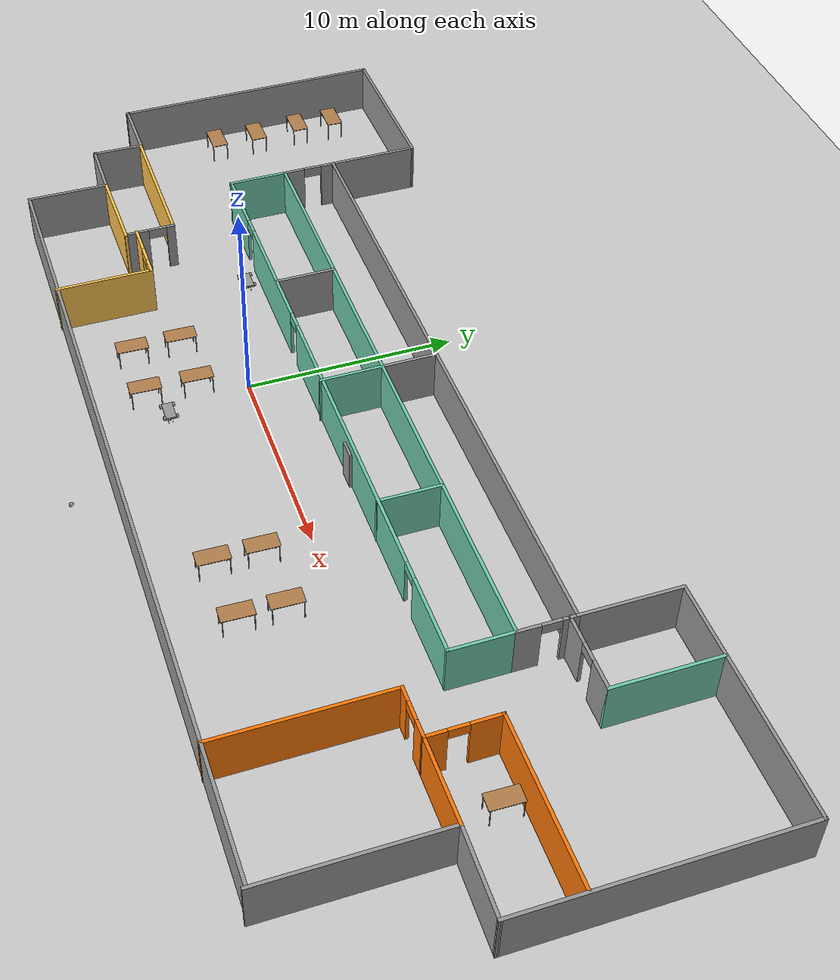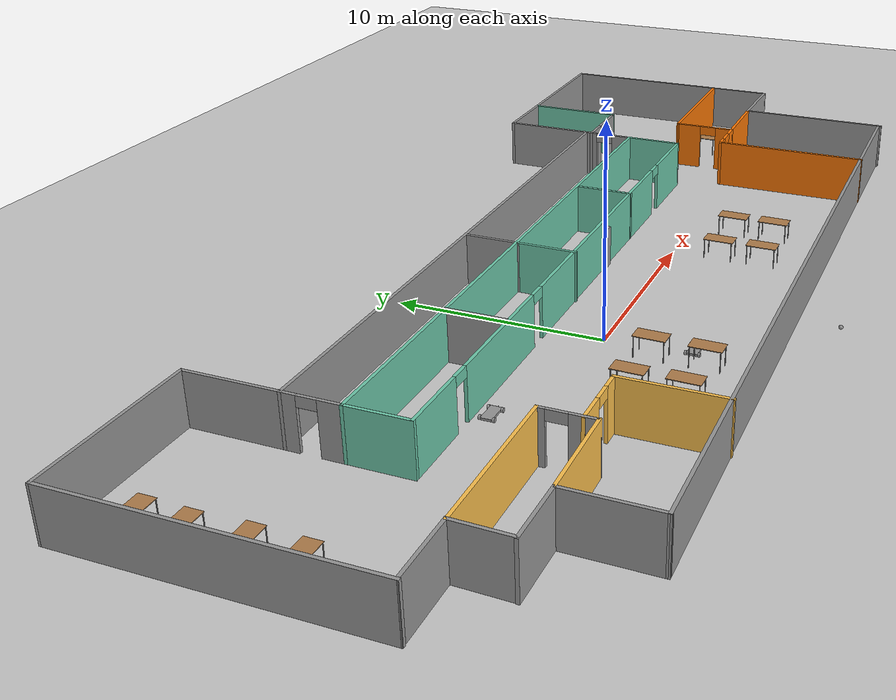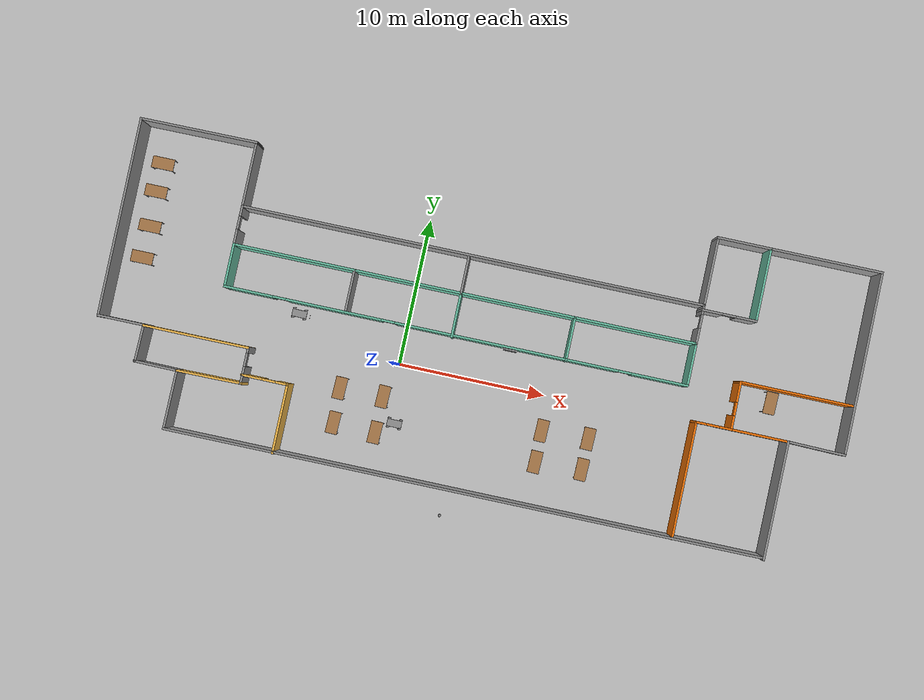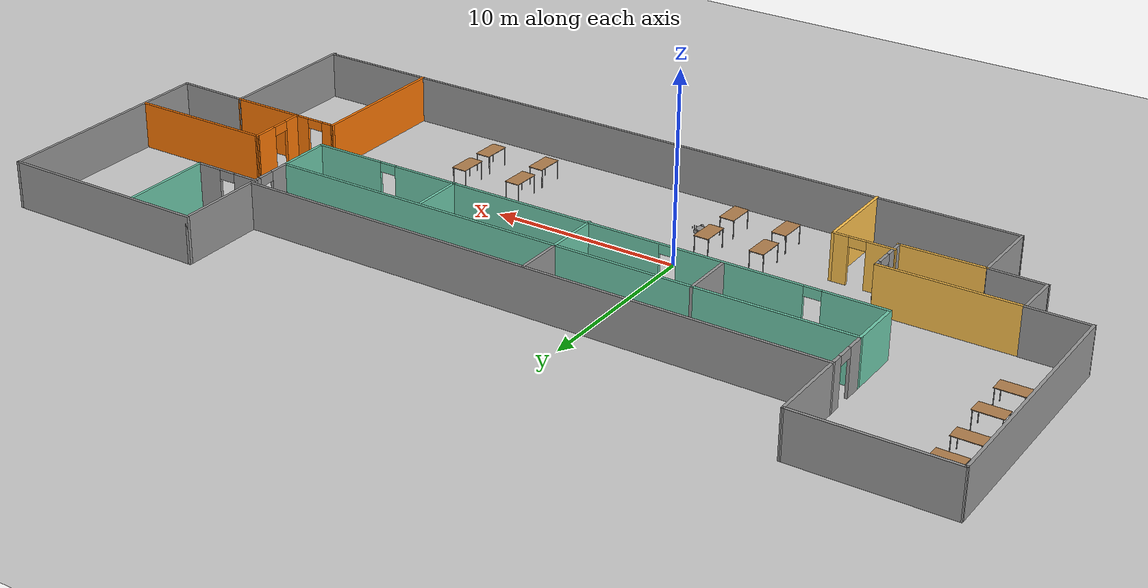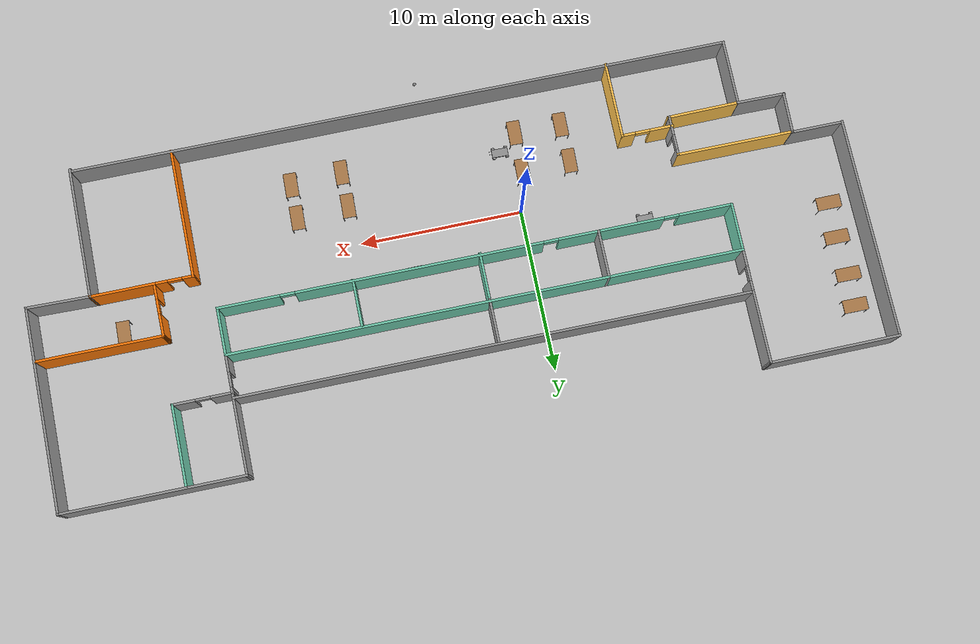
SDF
<sdf version="1.6">
 <world name="default">
  <plugin name="hello" filename="libhello.so"/>
  <light name="sun" type="directional">
   <pose>0 0 10 0 -0 0</pose>
   <diffuse>0.8 0.8 0.8 1</diffuse>
   <specular>0.2 0.2 0.2 1</specular>
   <attenuation>
    <range>1000</range>
    <constant>0.9</constant>
    <linear>0.01</linear>
    <quadratic>0.001</quadratic>
   </attenuation>
   <direction>-0.5 0.1 -0.9</direction>
  </light>
  <model name="ground_plane">
   <static>1</static>
   <link name="link">
    <collision name="collision">
     <geometry><plane><normal>0 0 1</normal><size>100 100</size></plane></geometry>
     <surface>
      <contact><collide_bitmask>65535</collide_bitmask></contact>
      <friction><ode><mu>100</mu><mu2>50</mu2></ode></friction>
     </surface>
    </collision>
    <visual name="visual">
     <cast_shadows>0</cast_shadows>
     <geometry><plane><normal>0 0 1</normal><size>100 100</size></plane></geometry>
     <material>
      <script><uri>file://media/materials/scripts/gazebo.material</uri><name>Gazebo/Grey</name></script>
     </material>
    </visual>
   </link>
  </model>
  <gravity>0 0 -9.8</gravity>
  <magnetic_field>6e-06 2.3e-05 -4.2e-05</magnetic_field>
  <atmosphere type="adiabatic"/>
  <physics name="default_physics" default="0" type="ode">
   <max_step_size>0.001</max_step_size>
   <real_time_factor>1</real_time_factor>
   <real_time_update_rate>1000</real_time_update_rate>
  </physics>
  <scene><ambient>0.4 0.4 0.4 1</ambient><background>0.7 0.7 0.7 1</background><shadows>1</shadows></scene>
  <spherical_coordinates>
   <surface_model>EARTH_WGS84</surface_model>
   <latitude_deg>0</latitude_deg>
   <longitude_deg>0</longitude_deg>
   <elevation>0</elevation>
   <heading_deg>0</heading_deg>
  </spherical_coordinates>
  <model name="building">
   <model name="buildingEditorModel">
    <pose>5.31659 2.25421 0 0 -0 0</pose>
    <link name="Door_2">
     <collision name="Door_2_Collision">
      <geometry><box><size>0.9 0.17 2</size></box></geometry>
      <pose>0 0 1 0 -0 0</pose>
     </collision>
     <visual name="Door_2_Visual">
      <pose>0 0 1 0 -0 0</pose>
      <geometry><box><size>0.9 0.17 2</size></box></geometry>
      <material>
       <script><uri>file://media/materials/scripts/gazebo.material</uri><name>Gazebo/Grey</name></script>
      </material>
     </visual>
     <pose>2.1186 -0.056948 0 0 -0 0</pose>
    </link>
    <link name="Wall_12">
     <collision name="Wall_12_Collision">
      <geometry><box><size>11.25 0.15 2.5</size></box></geometry>
      <pose>0 0 1.25 0 -0 0</pose>
     </collision>
     <visual name="Wall_12_Visual">
      <pose>0 0 1.25 0 -0 0</pose>
      <geometry><box><size>11.25 0.15 2.5</size></box></geometry>
      <material>
       <script><uri>file://media/materials/scripts/gazebo.material</uri><name>Gazebo/Grey</name></script>
       <ambient>1 1 1 1</ambient>
      </material>
      <meta><layer>0</layer></meta>
     </visual>
     <pose>19.5996 10.1001 0 0 -0 3.14159</pose>
    </link>
    <link name="Wall_13">
     <collision name="Wall_13_Collision">
      <geometry><box><size>4.75 0.15 2.5</size></box></geometry>
      <pose>0 0 1.25 0 -0 0</pose>
     </collision>
     <visual name="Wall_13_Visual">
      <pose>0 0 1.25 0 -0 0</pose>
      <geometry><box><size>4.75 0.15 2.5</size></box></geometry>
      <material>
       <script><uri>file://media/materials/scripts/gazebo.material</uri><name>Gazebo/Grey</name></script>
       <ambient>1 1 1 1</ambient>
      </material>
      <meta><layer>0</layer></meta>
     </visual>
     <pose>14.0496 7.80012 0 0 -0 -1.5708</pose>
    </link>
    <link name="Wall_14">
     <collision name="Wall_14_Collision">
      <geometry><box><size>31.5 0.15 2.5</size></box></geometry>
      <pose>0 0 1.25 0 -0 0</pose>
     </collision>
     <visual name="Wall_14_Visual">
      <pose>0 0 1.25 0 -0 0</pose>
      <geometry><box><size>31.5 0.15 2.5</size></box></geometry>
      <material>
       <script><uri>file://media/materials/scripts/gazebo.material</uri><name>Gazebo/Grey</name></script>
       <ambient>1 1 1 1</ambient>
      </material>
      <meta><layer>0</layer></meta>
     </visual>
     <pose>-1.62541 5.50012 0 0 -0 3.14159</pose>
    </link>
    <link name="Wall_15">
     <collision name="Wall_15_Collision">
      <geometry><box><size>4.5 0.15 2.5</size></box></geometry>
      <pose>0 0 1.25 0 -0 0</pose>
     </collision>
     <visual name="Wall_15_Visual">
      <pose>0 0 1.25 0 -0 0</pose>
      <geometry><box><size>4.5 0.15 2.5</size></box></geometry>
      <material>
       <script><uri>file://media/materials/scripts/gazebo.material</uri><name>Gazebo/Grey</name></script>
       <ambient>1 1 1 1</ambient>
      </material>
      <meta><layer>0</layer></meta>
     </visual>
     <pose>-17.3004 7.67512 0 0 -0 1.5708</pose>
    </link>
    <link name="Wall_18">
     <collision name="Wall_18_Collision">
      <geometry><box><size>8.00016 0.15 2.5</size></box></geometry>
      <pose>0 0 1.25 0 -0 0</pose>
     </collision>
     <visual name="Wall_18_Visual">
      <pose>0 0 1.25 0 -0 0</pose>
      <geometry><box><size>8.00016 0.15 2.5</size></box></geometry>
      <material>
       <script><uri>file://media/materials/scripts/gazebo.material</uri><name>Gazebo/Grey</name></script>
       <ambient>1 1 1 1</ambient>
      </material>
      <meta><layer>0</layer></meta>
     </visual>
     <pose>-21.2254 9.82512 0 0 -0 0.006369</pose>
    </link>
    <link name="Wall_20">
     <pose>-17.3004 4.20012 0 0 -0 -1.5708</pose>
     <visual name="Wall_20_Visual_0">
      <pose>-1.00181 0 1.25 0 -0 0</pose>
      <geometry><box><size>0.746388 0.15 2.5</size></box></geometry>
      <material>
       <script><uri>file://media/materials/scripts/gazebo.material</uri><name>Gazebo/Grey</name></script>
       <ambient>1 1 1 1</ambient>
      </material>
      <meta><layer>0</layer></meta>
     </visual>
     <collision name="Wall_20_Collision_0">
      <geometry><box><size>0.746388 0.15 2.5</size></box></geometry>
      <pose>-1.00181 0 1.25 0 -0 0</pose>
     </collision>
     <visual name="Wall_20_Visual_1">
      <pose>0.823194 0 1.25 0 -0 0</pose>
      <geometry><box><size>1.10361 0.15 2.5</size></box></geometry>
      <material>
       <script><uri>file://media/materials/scripts/gazebo.material</uri><name>Gazebo/Grey</name></script>
       <ambient>1 1 1 1</ambient>
      </material>
      <meta><layer>0</layer></meta>
     </visual>
     <collision name="Wall_20_Collision_1">
      <geometry><box><size>1.10361 0.15 2.5</size></box></geometry>
      <pose>0.823194 0 1.25 0 -0 0</pose>
     </collision>
     <visual name="Wall_20_Visual_2">
      <pose>-0.178612 0 2.25 0 -0 0</pose>
      <geometry><box><size>0.9 0.15 0.5</size></box></geometry>
      <material>
       <script><uri>file://media/materials/scripts/gazebo.material</uri><name>Gazebo/Grey</name></script>
       <ambient>1 1 1 1</ambient>
      </material>
      <meta><layer>0</layer></meta>
     </visual>
     <collision name="Wall_20_Collision_2">
      <geometry><box><size>0.9 0.15 0.5</size></box></geometry>
      <pose>-0.178612 0 2.25 0 -0 0</pose>
     </collision>
    </link>
    <link name="Wall_21">
     <collision name="Wall_21_Collision">
      <geometry><box><size>31.5 0.15 2.5</size></box></geometry>
      <pose>0 0 1.25 0 -0 0</pose>
     </collision>
     <visual name="Wall_21_Visual">
      <pose>0 0 1.25 0 -0 0</pose>
      <geometry><box><size>31.5 0.15 2.5</size></box></geometry>
      <material>
       <script><uri>file://media/materials/scripts/gazebo.material</uri><name>Gazebo/Grey</name></script>
       <ambient>0.435294 0.796078 0.67451 1</ambient>
      </material>
      <meta><layer>0</layer></meta>
     </visual>
     <pose>-1.62541 2.90012 0 0 -0 0</pose>
    </link>
    <link name="Wall_22">
     <pose>14.0496 4.20012 0 0 -0 1.5708</pose>
     <visual name="Wall_22_Visual_0">
      <pose>-0.810224 0 1.25 0 -0 0</pose>
      <geometry><box><size>1.12955 0.15 2.5</size></box></geometry>
      <material>
       <script><uri>file://media/materials/scripts/gazebo.material</uri><name>Gazebo/Grey</name></script>
       <ambient>1 1 1 1</ambient>
      </material>
      <meta><layer>0</layer></meta>
     </visual>
     <collision name="Wall_22_Collision_0">
      <geometry><box><size>1.12955 0.15 2.5</size></box></geometry>
      <pose>-0.810224 0 1.25 0 -0 0</pose>
     </collision>
     <visual name="Wall_22_Visual_1">
      <pose>1.01478 0 1.25 0 -0 0</pose>
      <geometry><box><size>0.720448 0.15 2.5</size></box></geometry>
      <material>
       <script><uri>file://media/materials/scripts/gazebo.material</uri><name>Gazebo/Grey</name></script>
       <ambient>1 1 1 1</ambient>
      </material>
      <meta><layer>0</layer></meta>
     </visual>
     <collision name="Wall_22_Collision_1">
      <geometry><box><size>0.720448 0.15 2.5</size></box></geometry>
      <pose>1.01478 0 1.25 0 -0 0</pose>
     </collision>
     <visual name="Wall_22_Visual_2">
      <pose>0.204552 0 2.25 0 -0 0</pose>
      <geometry><box><size>0.9 0.15 0.5</size></box></geometry>
      <material>
       <script><uri>file://media/materials/scripts/gazebo.material</uri><name>Gazebo/Grey</name></script>
       <ambient>1 1 1 1</ambient>
      </material>
      <meta><layer>0</layer></meta>
     </visual>
     <collision name="Wall_22_Collision_2">
      <geometry><box><size>0.9 0.15 0.5</size></box></geometry>
      <pose>0.204552 0 2.25 0 -0 0</pose>
     </collision>
    </link>
    <link name="Wall_24">
     <collision name="Wall_24_Collision">
      <geometry><box><size>3 0.15 2.5</size></box></geometry>
      <pose>0 0 1.25 0 -0 0</pose>
     </collision>
     <visual name="Wall_24_Visual">
      <pose>0 0 1.25 0 -0 0</pose>
      <geometry><box><size>3 0.15 2.5</size></box></geometry>
      <material>
       <script><uri>file://media/materials/scripts/gazebo.material</uri><name>Gazebo/Grey</name></script>
       <ambient>0.435294 0.796078 0.67451 1</ambient>
      </material>
      <meta><layer>0</layer></meta>
     </visual>
     <pose>-17.3004 1.47512 0 0 -0 -1.5708</pose>
    </link>
    <link name="Wall_25">
     <pose>-1.62541 0.050122 0 0 -0 0</pose>
     <visual name="Wall_25_Visual_0">
      <pose>-14.0877 0 1.25 0 -0 0</pose>
      <geometry><box><size>3.32458 0.15 2.5</size></box></geometry>
      <material>
       <script><uri>file://media/materials/scripts/gazebo.material</uri><name>Gazebo/Grey</name></script>
       <ambient>0.435294 0.796078 0.67451 1</ambient>
      </material>
      <meta><layer>0</layer></meta>
     </visual>
     <collision name="Wall_25_Collision_0">
      <geometry><box><size>3.32458 0.15 2.5</size></box></geometry>
      <pose>-14.0877 0 1.25 0 -0 0</pose>
     </collision>
     <visual name="Wall_25_Visual_1">
      <pose>-8.27902 0 1.25 0 -0 0</pose>
      <geometry><box><size>6.4928 0.15 2.5</size></box></geometry>
      <material>
       <script><uri>file://media/materials/scripts/gazebo.material</uri><name>Gazebo/Grey</name></script>
       <ambient>0.435294 0.796078 0.67451 1</ambient>
      </material>
      <meta><layer>0</layer></meta>
     </visual>
     <collision name="Wall_25_Collision_1">
      <geometry><box><size>6.4928 0.15 2.5</size></box></geometry>
      <pose>-8.27902 0 1.25 0 -0 0</pose>
     </collision>
     <visual name="Wall_25_Visual_2">
      <pose>3.43273 0 1.25 0 -0 0</pose>
      <geometry><box><size>15.1307 0.15 2.5</size></box></geometry>
      <material>
       <script><uri>file://media/materials/scripts/gazebo.material</uri><name>Gazebo/Grey</name></script>
       <ambient>0.435294 0.796078 0.67451 1</ambient>
      </material>
      <meta><layer>0</layer></meta>
     </visual>
     <collision name="Wall_25_Collision_2">
      <geometry><box><size>15.1307 0.15 2.5</size></box></geometry>
      <pose>3.43273 0 1.25 0 -0 0</pose>
     </collision>
     <visual name="Wall_25_Visual_3">
      <pose>13.824 0 1.25 0 -0 0</pose>
      <geometry><box><size>3.85191 0.15 2.5</size></box></geometry>
      <material>
       <script><uri>file://media/materials/scripts/gazebo.material</uri><name>Gazebo/Grey</name></script>
       <ambient>0.435294 0.796078 0.67451 1</ambient>
      </material>
      <meta><layer>0</layer></meta>
     </visual>
     <collision name="Wall_25_Collision_3">
      <geometry><box><size>3.85191 0.15 2.5</size></box></geometry>
      <pose>13.824 0 1.25 0 -0 0</pose>
     </collision>
     <visual name="Wall_25_Visual_4">
      <pose>-11.9754 0 2.25 0 -0 0</pose>
      <geometry><box><size>0.9 0.15 0.5</size></box></geometry>
      <material>
       <script><uri>file://media/materials/scripts/gazebo.material</uri><name>Gazebo/Grey</name></script>
       <ambient>0.435294 0.796078 0.67451 1</ambient>
      </material>
      <meta><layer>0</layer></meta>
     </visual>
     <collision name="Wall_25_Collision_4">
      <geometry><box><size>0.9 0.15 0.5</size></box></geometry>
      <pose>-11.9754 0 2.25 0 -0 0</pose>
     </collision>
     <visual name="Wall_25_Visual_5">
      <pose>-4.58262 0 2.25 0 -0 0</pose>
      <geometry><box><size>0.9 0.15 0.5</size></box></geometry>
      <material>
       <script><uri>file://media/materials/scripts/gazebo.material</uri><name>Gazebo/Grey</name></script>
       <ambient>0.435294 0.796078 0.67451 1</ambient>
      </material>
      <meta><layer>0</layer></meta>
     </visual>
     <collision name="Wall_25_Collision_5">
      <geometry><box><size>0.9 0.15 0.5</size></box></geometry>
      <pose>-4.58262 0 2.25 0 -0 0</pose>
     </collision>
     <visual name="Wall_25_Visual_6">
      <pose>11.4481 0 2.25 0 -0 0</pose>
      <geometry><box><size>0.9 0.15 0.5</size></box></geometry>
      <material>
       <script><uri>file://media/materials/scripts/gazebo.material</uri><name>Gazebo/Grey</name></script>
       <ambient>0.435294 0.796078 0.67451 1</ambient>
      </material>
      <meta><layer>0</layer></meta>
     </visual>
     <collision name="Wall_25_Collision_6">
      <geometry><box><size>0.9 0.15 0.5</size></box></geometry>
      <pose>11.4481 0 2.25 0 -0 0</pose>
     </collision>
    </link>
    <link name="Wall_26">
     <collision name="Wall_26_Collision">
      <geometry><box><size>3 0.15 2.5</size></box></geometry>
      <pose>0 0 1.25 0 -0 0</pose>
     </collision>
     <visual name="Wall_26_Visual">
      <pose>0 0 1.25 0 -0 0</pose>
      <geometry><box><size>3 0.15 2.5</size></box></geometry>
      <material>
       <script><uri>file://media/materials/scripts/gazebo.material</uri><name>Gazebo/Grey</name></script>
       <ambient>0.435294 0.796078 0.67451 1</ambient>
      </material>
      <meta><layer>0</layer></meta>
     </visual>
     <pose>14.0496 1.47512 0 0 -0 1.5708</pose>
    </link>
    <link name="Wall_28">
     <collision name="Wall_28_Collision">
      <geometry><box><size>2.75 0.15 2.5</size></box></geometry>
      <pose>0 0 1.25 0 -0 0</pose>
     </collision>
     <visual name="Wall_28_Visual">
      <pose>0 0 1.25 0 -0 0</pose>
      <geometry><box><size>2.75 0.15 2.5</size></box></geometry>
      <material>
       <script><uri>file://media/materials/scripts/gazebo.material</uri><name>Gazebo/Grey</name></script>
       <ambient>1 1 1 1</ambient>
      </material>
      <meta><layer>0</layer></meta>
     </visual>
     <pose>-1.8761 4.11632 0 0 -0 -1.5708</pose>
    </link>
    <link name="Wall_30">
     <collision name="Wall_30_Collision">
      <geometry><box><size>3 0.15 2.5</size></box></geometry>
      <pose>0 0 1.25 0 -0 0</pose>
     </collision>
     <visual name="Wall_30_Visual">
      <pose>0 0 1.25 0 -0 0</pose>
      <geometry><box><size>3 0.15 2.5</size></box></geometry>
      <material>
       <script><uri>file://media/materials/scripts/gazebo.material</uri><name>Gazebo/Grey</name></script>
       <ambient>1 1 1 1</ambient>
      </material>
      <meta><layer>0</layer></meta>
     </visual>
     <pose>-9.11327 1.47517 0 0 -0 -1.5708</pose>
    </link>
    <link name="Wall_34">
     <collision name="Wall_34_Collision">
      <geometry><box><size>3 0.15 2.5</size></box></geometry>
      <pose>0 0 1.25 0 -0 0</pose>
     </collision>
     <visual name="Wall_34_Visual">
      <pose>0 0 1.25 0 -0 0</pose>
      <geometry><box><size>3 0.15 2.5</size></box></geometry>
      <material>
       <script><uri>file://media/materials/scripts/gazebo.material</uri><name>Gazebo/Grey</name></script>
       <ambient>0.435294 0.796078 0.67451 1</ambient>
      </material>
      <meta><layer>0</layer></meta>
     </visual>
     <pose>-1.8761 1.39132 0 0 -0 -1.5708</pose>
    </link>
    <link name="Wall_36">
     <collision name="Wall_36_Collision">
      <geometry><box><size>3 0.15 2.5</size></box></geometry>
      <pose>0 0 1.25 0 -0 0</pose>
     </collision>
     <visual name="Wall_36_Visual">
      <pose>0 0 1.25 0 -0 0</pose>
      <geometry><box><size>3 0.15 2.5</size></box></geometry>
      <material>
       <script><uri>file://media/materials/scripts/gazebo.material</uri><name>Gazebo/Grey</name></script>
       <ambient>0.435294 0.796078 0.67451 1</ambient>
      </material>
      <meta><layer>0</layer></meta>
     </visual>
     <pose>5.85391 1.44923 0 0 -0 -1.5708</pose>
    </link>
    <link name="Wall_38">
     <collision name="Wall_38_Collision">
      <geometry><box><size>12.5 0.15 2.5</size></box></geometry>
      <pose>0 0 1.25 0 -0 0</pose>
     </collision>
     <visual name="Wall_38_Visual">
      <pose>0 0 1.25 0 -0 0</pose>
      <geometry><box><size>12.5 0.15 2.5</size></box></geometry>
      <material>
       <script><uri>file://media/materials/scripts/gazebo.material</uri><name>Gazebo/Grey</name></script>
       <ambient>1 1 1 1</ambient>
      </material>
      <meta><layer>0</layer></meta>
     </visual>
     <pose>25.1496 3.92512 0 0 -0 -1.5708</pose>
    </link>
    <link name="Wall_39">
     <collision name="Wall_39_Collision">
      <geometry><box><size>3.97441 0.15 2.5</size></box></geometry>
      <pose>0 0 1.25 0 -0 0</pose>
     </collision>
     <visual name="Wall_39_Visual">
      <pose>0 0 1.25 0 -0 0</pose>
      <geometry><box><size>3.97441 0.15 2.5</size></box></geometry>
      <material>
       <script><uri>file://media/materials/scripts/gazebo.material</uri><name>Gazebo/Grey</name></script>
       <ambient>1 1 1 1</ambient>
      </material>
      <meta><layer>0</layer></meta>
     </visual>
     <pose>23.2376 -2.21097 0 0 -0 3.12125</pose>
    </link>
    <link name="Wall_40">
     <collision name="Wall_40_Collision">
      <geometry><box><size>8.07786 0.15 2.5</size></box></geometry>
      <pose>0 0 1.25 0 -0 0</pose>
     </collision>
     <visual name="Wall_40_Visual">
      <pose>0 0 1.25 0 -0 0</pose>
      <geometry><box><size>8.07786 0.15 2.5</size></box></geometry>
      <material>
       <script><uri>file://media/materials/scripts/gazebo.material</uri><name>Gazebo/Grey</name></script>
       <ambient>1 1 1 1</ambient>
      </material>
      <meta><layer>0</layer></meta>
     </visual>
     <pose>21.3126 -6.13597 0 0 -0 -1.57407</pose>
    </link>
    <link name="Wall_42">
     <collision name="Wall_42_Collision">
      <geometry><box><size>40.5 0.15 2.5</size></box></geometry>
      <pose>0 0 1.25 0 -0 0</pose>
     </collision>
     <visual name="Wall_42_Visual">
      <pose>0 0 1.25 0 -0 0</pose>
      <geometry><box><size>40.5 0.15 2.5</size></box></geometry>
      <material>
       <script><uri>file://media/materials/scripts/gazebo.material</uri><name>Gazebo/Grey</name></script>
       <ambient>1 1 1 1</ambient>
      </material>
      <meta><layer>0</layer></meta>
     </visual>
     <pose>0.974593 -9.99988 0 0 -0 0</pose>
    </link>
    <link name="Wall_45">
     <collision name="Wall_45_Collision">
      <geometry><box><size>7.25 0.15 2.5</size></box></geometry>
      <pose>0 0 1.25 0 -0 0</pose>
     </collision>
     <visual name="Wall_45_Visual">
      <pose>0 0 1.25 0 -0 0</pose>
      <geometry><box><size>7.25 0.15 2.5</size></box></geometry>
      <material>
       <script><uri>file://media/materials/scripts/gazebo.material</uri><name>Gazebo/Grey</name></script>
       <ambient>1 0.764706 0.305882 1</ambient>
      </material>
      <meta><layer>0</layer></meta>
     </visual>
     <pose>-18.4226 -3.61565 0 0 -0 0</pose>
    </link>
    <link name="Wall_46">
     <pose>-14.8726 -4.81659 0 0 -0 -1.5708</pose>
     <visual name="Wall_46_Visual_0">
      <pose>-1.06386 0 1.25 0 -0 0</pose>
      <geometry><box><size>0.424155 0.15 2.5</size></box></geometry>
      <material>
       <script><uri>file://media/materials/scripts/gazebo.material</uri><name>Gazebo/Grey</name></script>
       <ambient>1 1 1 1</ambient>
      </material>
      <meta><layer>0</layer></meta>
     </visual>
     <collision name="Wall_46_Collision_0">
      <geometry><box><size>0.424155 0.15 2.5</size></box></geometry>
      <pose>-1.06386 0 1.25 0 -0 0</pose>
     </collision>
     <visual name="Wall_46_Visual_1">
      <pose>0.662078 0 1.25 0 -0 0</pose>
      <geometry><box><size>1.22772 0.15 2.5</size></box></geometry>
      <material>
       <script><uri>file://media/materials/scripts/gazebo.material</uri><name>Gazebo/Grey</name></script>
       <ambient>1 1 1 1</ambient>
      </material>
      <meta><layer>0</layer></meta>
     </visual>
     <collision name="Wall_46_Collision_1">
      <geometry><box><size>1.22772 0.15 2.5</size></box></geometry>
      <pose>0.662078 0 1.25 0 -0 0</pose>
     </collision>
     <visual name="Wall_46_Visual_2">
      <pose>-0.401784 0 2.25 0 -0 0</pose>
      <geometry><box><size>0.9 0.15 0.5</size></box></geometry>
      <material>
       <script><uri>file://media/materials/scripts/gazebo.material</uri><name>Gazebo/Grey</name></script>
       <ambient>1 1 1 1</ambient>
      </material>
      <meta><layer>0</layer></meta>
     </visual>
     <collision name="Wall_46_Collision_2">
      <geometry><box><size>0.9 0.15 0.5</size></box></geometry>
      <pose>-0.401784 0 2.25 0 -0 0</pose>
     </collision>
    </link>
    <link name="Wall_47">
     <collision name="Wall_47_Collision">
      <geometry><box><size>4.45217 0.15 2.5</size></box></geometry>
      <pose>0 0 1.25 0 -0 0</pose>
     </collision>
     <visual name="Wall_47_Visual">
      <pose>0 0 1.25 0 -0 0</pose>
      <geometry><box><size>4.45217 0.15 2.5</size></box></geometry>
      <material>
       <script><uri>file://media/materials/scripts/gazebo.material</uri><name>Gazebo/Grey</name></script>
       <ambient>1 0.764706 0.305882 1</ambient>
      </material>
      <meta><layer>0</layer></meta>
     </visual>
     <pose>-16.9976 -6.04235 0 0 -0 -3.13006</pose>
    </link>
    <link name="Wall_5">
     <collision name="Wall_5_Collision">
      <geometry><box><size>13.566 0.15 2.5</size></box></geometry>
      <pose>0 0 1.25 0 -0 0</pose>
     </collision>
     <visual name="Wall_5_Visual">
      <pose>0 0 1.25 0 -0 0</pose>
      <geometry><box><size>13.566 0.15 2.5</size></box></geometry>
      <material>
       <script><uri>file://media/materials/scripts/gazebo.material</uri><name>Gazebo/Grey</name></script>
       <ambient>1 1 1 1</ambient>
      </material>
      <meta><layer>0</layer></meta>
     </visual>
     <pose>-25.1115 3.09223 0 0 -0 -1.565</pose>
    </link>
    <link name="Wall_51">
     <pose>-13.3738 -5.4524 0 0 -0 0</pose>
     <visual name="Wall_51_Visual_0">
      <pose>-0.891642 0 1.25 0 -0 0</pose>
      <geometry><box><size>1.46672 0.15 2.5</size></box></geometry>
      <material>
       <script><uri>file://media/materials/scripts/gazebo.material</uri><name>Gazebo/Grey</name></script>
       <ambient>1 0.764706 0.305882 1</ambient>
      </material>
      <meta><layer>0</layer></meta>
     </visual>
     <collision name="Wall_51_Collision_0">
      <geometry><box><size>1.46672 0.15 2.5</size></box></geometry>
      <pose>-0.891642 0 1.25 0 -0 0</pose>
     </collision>
     <visual name="Wall_51_Visual_1">
      <pose>1.18336 0 1.25 0 -0 0</pose>
      <geometry><box><size>0.883284 0.15 2.5</size></box></geometry>
      <material>
       <script><uri>file://media/materials/scripts/gazebo.material</uri><name>Gazebo/Grey</name></script>
       <ambient>1 0.764706 0.305882 1</ambient>
      </material>
      <meta><layer>0</layer></meta>
     </visual>
     <collision name="Wall_51_Collision_1">
      <geometry><box><size>0.883284 0.15 2.5</size></box></geometry>
      <pose>1.18336 0 1.25 0 -0 0</pose>
     </collision>
     <visual name="Wall_51_Visual_2">
      <pose>0.291716 0 2.25 0 -0 0</pose>
      <geometry><box><size>0.9 0.15 0.5</size></box></geometry>
      <material>
       <script><uri>file://media/materials/scripts/gazebo.material</uri><name>Gazebo/Grey</name></script>
       <ambient>1 0.764706 0.305882 1</ambient>
      </material>
      <meta><layer>0</layer></meta>
     </visual>
     <collision name="Wall_51_Collision_2">
      <geometry><box><size>0.9 0.15 0.5</size></box></geometry>
      <pose>0.291716 0 2.25 0 -0 0</pose>
     </collision>
    </link>
    <link name="Wall_52">
     <collision name="Wall_52_Collision">
      <geometry><box><size>4.75 0.15 2.5</size></box></geometry>
      <pose>0 0 1.25 0 -0 0</pose>
     </collision>
     <visual name="Wall_52_Visual">
      <pose>0 0 1.25 0 -0 0</pose>
      <geometry><box><size>4.75 0.15 2.5</size></box></geometry>
      <material>
       <script><uri>file://media/materials/scripts/gazebo.material</uri><name>Gazebo/Grey</name></script>
       <ambient>1 0.764706 0.305882 1</ambient>
      </material>
      <meta><layer>0</layer></meta>
     </visual>
     <pose>-11.8238 -7.7524 0 0 -0 -1.5708</pose>
    </link>
    <link name="Wall_54">
     <collision name="Wall_54_Collision">
      <geometry><box><size>7.75 0.15 2.5</size></box></geometry>
      <pose>0 0 1.25 0 -0 0</pose>
     </collision>
     <visual name="Wall_54_Visual">
      <pose>0 0 1.25 0 -0 0</pose>
      <geometry><box><size>7.75 0.15 2.5</size></box></geometry>
      <material>
       <script><uri>file://media/materials/scripts/gazebo.material</uri><name>Gazebo/Grey</name></script>
       <ambient>0.996078 0.47451 0.0196078 1</ambient>
      </material>
      <meta><layer>0</layer></meta>
     </visual>
     <pose>21.2493 1.03252 0 0 -0 3.14159</pose>
    </link>
    <link name="Wall_58">
     <collision name="Wall_58_Collision">
      <geometry><box><size>4 0.15 2.5</size></box></geometry>
      <pose>0 0 1.25 0 -0 0</pose>
     </collision>
     <visual name="Wall_58_Visual">
      <pose>0 0 1.25 0 -0 0</pose>
      <geometry><box><size>4 0.15 2.5</size></box></geometry>
      <material>
       <script><uri>file://media/materials/scripts/gazebo.material</uri><name>Gazebo/Grey</name></script>
       <ambient>0.996078 0.47451 0.0196078 1</ambient>
      </material>
      <meta><layer>0</layer></meta>
     </visual>
     <pose>19.4005 -2.17206 0 0 -0 3.14159</pose>
    </link>
    <link name="Wall_59">
     <pose>17.4624 -0.569771 0 0 -0 1.57899</pose>
     <visual name="Wall_59_Visual_0">
      <pose>-1.17025 0 1.25 0 -0 0</pose>
      <geometry><box><size>1.01419 0.15 2.5</size></box></geometry>
      <material>
       <script><uri>file://media/materials/scripts/gazebo.material</uri><name>Gazebo/Grey</name></script>
       <ambient>0.996078 0.47451 0.0196078 1</ambient>
      </material>
      <meta><layer>0</layer></meta>
     </visual>
     <collision name="Wall_59_Collision_0">
      <geometry><box><size>1.01419 0.15 2.5</size></box></geometry>
      <pose>-1.17025 0 1.25 0 -0 0</pose>
     </collision>
     <visual name="Wall_59_Visual_1">
      <pose>0.957093 0 1.25 0 -0 0</pose>
      <geometry><box><size>1.4405 0.15 2.5</size></box></geometry>
      <material>
       <script><uri>file://media/materials/scripts/gazebo.material</uri><name>Gazebo/Grey</name></script>
       <ambient>0.996078 0.47451 0.0196078 1</ambient>
      </material>
      <meta><layer>0</layer></meta>
     </visual>
     <collision name="Wall_59_Collision_1">
      <geometry><box><size>1.4405 0.15 2.5</size></box></geometry>
      <pose>0.957093 0 1.25 0 -0 0</pose>
     </collision>
     <visual name="Wall_59_Visual_2">
      <pose>-0.213157 0 2.25 0 -0 0</pose>
      <geometry><box><size>0.9 0.15 0.5</size></box></geometry>
      <material>
       <script><uri>file://media/materials/scripts/gazebo.material</uri><name>Gazebo/Grey</name></script>
       <ambient>0.996078 0.47451 0.0196078 1</ambient>
      </material>
      <meta><layer>0</layer></meta>
     </visual>
     <collision name="Wall_59_Collision_2">
      <geometry><box><size>0.9 0.15 0.5</size></box></geometry>
      <pose>-0.213157 0 2.25 0 -0 0</pose>
     </collision>
    </link>
    <link name="Wall_6">
     <collision name="Wall_6_Collision">
      <geometry><box><size>3.25 0.15 2.5</size></box></geometry>
      <pose>0 0 1.25 0 -0 0</pose>
     </collision>
     <visual name="Wall_6_Visual">
      <pose>0 0 1.25 0 -0 0</pose>
      <geometry><box><size>3.25 0.15 2.5</size></box></geometry>
      <material>
       <script><uri>file://media/materials/scripts/gazebo.material</uri><name>Gazebo/Grey</name></script>
       <ambient>1 1 1 1</ambient>
      </material>
      <meta><layer>0</layer></meta>
     </visual>
     <pose>-23.5226 -3.58971 0 0 -0 0</pose>
    </link>
    <link name="Wall_62">
     <pose>16.3005 -2.17206 0 0 -0 3.14159</pose>
     <visual name="Wall_62_Visual_0">
      <pose>-0.814621 0 1.25 0 -0 0</pose>
      <geometry><box><size>0.870759 0.15 2.5</size></box></geometry>
      <material>
       <script><uri>file://media/materials/scripts/gazebo.material</uri><name>Gazebo/Grey</name></script>
       <ambient>0.996078 0.47451 0.0196078 1</ambient>
      </material>
      <meta><layer>0</layer></meta>
     </visual>
     <collision name="Wall_62_Collision_0">
      <geometry><box><size>0.870759 0.15 2.5</size></box></geometry>
      <pose>-0.814621 0 1.25 0 -0 0</pose>
     </collision>
     <visual name="Wall_62_Visual_1">
      <pose>0.885379 0 1.25 0 -0 0</pose>
      <geometry><box><size>0.729241 0.15 2.5</size></box></geometry>
      <material>
       <script><uri>file://media/materials/scripts/gazebo.material</uri><name>Gazebo/Grey</name></script>
       <ambient>0.996078 0.47451 0.0196078 1</ambient>
      </material>
      <meta><layer>0</layer></meta>
     </visual>
     <collision name="Wall_62_Collision_1">
      <geometry><box><size>0.729241 0.15 2.5</size></box></geometry>
      <pose>0.885379 0 1.25 0 -0 0</pose>
     </collision>
     <visual name="Wall_62_Visual_2">
      <pose>0.070759 0 2.25 0 -0 0</pose>
      <geometry><box><size>0.9 0.15 0.5</size></box></geometry>
      <material>
       <script><uri>file://media/materials/scripts/gazebo.material</uri><name>Gazebo/Grey</name></script>
       <ambient>0.996078 0.47451 0.0196078 1</ambient>
      </material>
      <meta><layer>0</layer></meta>
     </visual>
     <collision name="Wall_62_Collision_2">
      <geometry><box><size>0.9 0.15 0.5</size></box></geometry>
      <pose>0.070759 0 2.25 0 -0 0</pose>
     </collision>
    </link>
    <link name="Wall_63">
     <collision name="Wall_63_Collision">
      <geometry><box><size>8 0.15 2.5</size></box></geometry>
      <pose>0 0 1.25 0 -0 0</pose>
     </collision>
     <visual name="Wall_63_Visual">
      <pose>0 0 1.25 0 -0 0</pose>
      <geometry><box><size>8 0.15 2.5</size></box></geometry>
      <material>
       <script><uri>file://media/materials/scripts/gazebo.material</uri><name>Gazebo/Grey</name></script>
       <ambient>0.996078 0.47451 0.0196078 1</ambient>
      </material>
      <meta><layer>0</layer></meta>
     </visual>
     <pose>15.1255 -6.09706 0 0 -0 -1.5708</pose>
    </link>
    <link name="Wall_65">
     <pose>15.8249 5.18286 0 0 -0 0</pose>
     <visual name="Wall_65_Visual_0">
      <pose>-1.16758 0 1.25 0 -0 0</pose>
      <geometry><box><size>1.41484 0.15 2.5</size></box></geometry>
      <material>
       <script><uri>file://media/materials/scripts/gazebo.material</uri><name>Gazebo/Grey</name></script>
       <ambient>1 1 1 1</ambient>
      </material>
      <meta><layer>0</layer></meta>
     </visual>
     <collision name="Wall_65_Collision_0">
      <geometry><box><size>1.41484 0.15 2.5</size></box></geometry>
      <pose>-1.16758 0 1.25 0 -0 0</pose>
     </collision>
     <visual name="Wall_65_Visual_1">
      <pose>1.15742 0 1.25 0 -0 0</pose>
      <geometry><box><size>1.43516 0.15 2.5</size></box></geometry>
      <material>
       <script><uri>file://media/materials/scripts/gazebo.material</uri><name>Gazebo/Grey</name></script>
       <ambient>1 1 1 1</ambient>
      </material>
      <meta><layer>0</layer></meta>
     </visual>
     <collision name="Wall_65_Collision_1">
      <geometry><box><size>1.43516 0.15 2.5</size></box></geometry>
      <pose>1.15742 0 1.25 0 -0 0</pose>
     </collision>
     <visual name="Wall_65_Visual_2">
      <pose>-0.010162 0 2.25 0 -0 0</pose>
      <geometry><box><size>0.9 0.15 0.5</size></box></geometry>
      <material>
       <script><uri>file://media/materials/scripts/gazebo.material</uri><name>Gazebo/Grey</name></script>
       <ambient>1 1 1 1</ambient>
      </material>
      <meta><layer>0</layer></meta>
     </visual>
     <collision name="Wall_65_Collision_2">
      <geometry><box><size>0.9 0.15 0.5</size></box></geometry>
      <pose>-0.010162 0 2.25 0 -0 0</pose>
     </collision>
    </link>
    <link name="Wall_66">
     <collision name="Wall_66_Collision">
      <geometry><box><size>5 0.15 2.5</size></box></geometry>
      <pose>0 0 1.25 0 -0 0</pose>
     </collision>
     <visual name="Wall_66_Visual">
      <pose>0 0 1.25 0 -0 0</pose>
      <geometry><box><size>5 0.15 2.5</size></box></geometry>
      <material>
       <script><uri>file://media/materials/scripts/gazebo.material</uri><name>Gazebo/Grey</name></script>
       <ambient>0.435294 0.796078 0.67451 1</ambient>
      </material>
      <meta><layer>0</layer></meta>
     </visual>
     <pose>17.6249 7.60786 0 0 -0 1.5708</pose>
    </link>
    <link name="Wall_7">
     <collision name="Wall_7_Collision">
      <geometry><box><size>2.55019 0.15 2.5</size></box></geometry>
      <pose>0 0 1.25 0 -0 0</pose>
     </collision>
     <visual name="Wall_7_Visual">
      <pose>0 0 1.25 0 -0 0</pose>
      <geometry><box><size>2.55019 0.15 2.5</size></box></geometry>
      <material>
       <script><uri>file://media/materials/scripts/gazebo.material</uri><name>Gazebo/Grey</name></script>
       <ambient>1 1 1 1</ambient>
      </material>
      <meta><layer>0</layer></meta>
     </visual>
     <pose>-21.9985 -4.81547 0 0 -0 -1.59241</pose>
    </link>
    <link name="Wall_8">
     <collision name="Wall_8_Collision">
      <geometry><box><size>3.02606 0.15 2.5</size></box></geometry>
      <pose>0 0 1.25 0 -0 0</pose>
     </collision>
     <visual name="Wall_8_Visual">
      <pose>0 0 1.25 0 -0 0</pose>
      <geometry><box><size>3.02606 0.15 2.5</size></box></geometry>
      <material>
       <script><uri>file://media/materials/scripts/gazebo.material</uri><name>Gazebo/Grey</name></script>
       <ambient>1 1 1 1</ambient>
      </material>
      <meta><layer>0</layer></meta>
     </visual>
     <pose>-20.6124 -6.05419 0 0 -0 -0.009019</pose>
    </link>
    <link name="Wall_9">
     <collision name="Wall_9_Collision">
      <geometry><box><size>4.0828 0.15 2.5</size></box></geometry>
      <pose>0 0 1.25 0 -0 0</pose>
     </collision>
     <visual name="Wall_9_Visual">
      <pose>0 0 1.25 0 -0 0</pose>
      <geometry><box><size>4.0828 0.15 2.5</size></box></geometry>
      <material>
       <script><uri>file://media/materials/scripts/gazebo.material</uri><name>Gazebo/Grey</name></script>
       <ambient>1 1 1 1</ambient>
      </material>
      <meta><layer>0</layer></meta>
     </visual>
     <pose>-19.1874 -8.03352 0 0 -0 -1.57739</pose>
    </link>
    <static>1</static>
   </model>
   <model name="table">
    <static>1</static>
    <link name="link">
     <collision name="surface">
      <pose>0 0 1 0 -0 0</pose>
      <geometry><box><size>1.5 0.8 0.03</size></box></geometry>
      <surface><friction><ode><mu>0.6</mu><mu2>0.6</mu2></ode></friction></surface>
     </collision>
     <visual name="visual1">
      <pose>0 0 1 0 -0 0</pose>
      <geometry><box><size>1.5 0.8 0.03</size></box></geometry>
      <material>
       <script><uri>file://media/materials/scripts/gazebo.material</uri><name>Gazebo/Wood</name></script>
      </material>
     </visual>
     <collision name="front_left_leg">
      <pose>0.68 0.38 0.5 0 -0 0</pose>
      <geometry><cylinder><radius>0.02</radius><length>1</length></cylinder></geometry>
     </collision>
     <visual name="front_left_leg">
      <pose>0.68 0.38 0.5 0 -0 0</pose>
      <geometry><cylinder><radius>0.02</radius><length>1</length></cylinder></geometry>
      <material>
       <script><uri>file://media/materials/scripts/gazebo.material</uri><name>Gazebo/Grey</name></script>
      </material>
     </visual>
     <collision name="front_right_leg">
      <pose>0.68 -0.38 0.5 0 -0 0</pose>
      <geometry><cylinder><radius>0.02</radius><length>1</length></cylinder></geometry>
     </collision>
     <visual name="front_right_leg">
      <pose>0.68 -0.38 0.5 0 -0 0</pose>
      <geometry><cylinder><radius>0.02</radius><length>1</length></cylinder></geometry>
      <material>
       <script><uri>file://media/materials/scripts/gazebo.material</uri><name>Gazebo/Grey</name></script>
      </material>
     </visual>
     <collision name="back_right_leg">
      <pose>-0.68 -0.38 0.5 0 -0 0</pose>
      <geometry><cylinder><radius>0.02</radius><length>1</length></cylinder></geometry>
     </collision>
     <visual name="back_right_leg">
      <pose>-0.68 -0.38 0.5 0 -0 0</pose>
      <geometry><cylinder><radius>0.02</radius><length>1</length></cylinder></geometry>
      <material>
       <script><uri>file://media/materials/scripts/gazebo.material</uri><name>Gazebo/Grey</name></script>
      </material>
     </visual>
     <collision name="back_left_leg">
      <pose>-0.68 0.38 0.5 0 -0 0</pose>
      <geometry><cylinder><radius>0.02</radius><length>1</length></cylinder></geometry>
     </collision>
     <visual name="back_left_leg">
      <pose>-0.68 0.38 0.5 0 -0 0</pose>
      <geometry><cylinder><radius>0.02</radius><length>1</length></cylinder></geometry>
      <material>
       <script><uri>file://media/materials/scripts/gazebo.material</uri><name>Gazebo/Grey</name></script>
      </material>
     </visual>
    </link>
    <pose>-18.1294 9.58037 0 0 -0 0</pose>
   </model>
   <model name="table_0">
    <static>1</static>
    <link name="link">
     <collision name="surface">
      <pose>0 0 1 0 -0 0</pose>
      <geometry><box><size>1.5 0.8 0.03</size></box></geometry>
      <surface><friction><ode><mu>0.6</mu><mu2>0.6</mu2></ode></friction></surface>
     </collision>
     <visual name="visual1">
      <pose>0 0 1 0 -0 0</pose>
      <geometry><box><size>1.5 0.8 0.03</size></box></geometry>
      <material>
       <script><uri>file://media/materials/scripts/gazebo.material</uri><name>Gazebo/Wood</name></script>
      </material>
     </visual>
     <collision name="front_left_leg">
      <pose>0.68 0.38 0.5 0 -0 0</pose>
      <geometry><cylinder><radius>0.02</radius><length>1</length></cylinder></geometry>
     </collision>
     <visual name="front_left_leg">
      <pose>0.68 0.38 0.5 0 -0 0</pose>
      <geometry><cylinder><radius>0.02</radius><length>1</length></cylinder></geometry>
      <material>
       <script><uri>file://media/materials/scripts/gazebo.material</uri><name>Gazebo/Grey</name></script>
      </material>
     </visual>
     <collision name="front_right_leg">
      <pose>0.68 -0.38 0.5 0 -0 0</pose>
      <geometry><cylinder><radius>0.02</radius><length>1</length></cylinder></geometry>
     </collision>
     <visual name="front_right_leg">
      <pose>0.68 -0.38 0.5 0 -0 0</pose>
      <geometry><cylinder><radius>0.02</radius><length>1</length></cylinder></geometry>
      <material>
       <script><uri>file://media/materials/scripts/gazebo.material</uri><name>Gazebo/Grey</name></script>
      </material>
     </visual>
     <collision name="back_right_leg">
      <pose>-0.68 -0.38 0.5 0 -0 0</pose>
      <geometry><cylinder><radius>0.02</radius><length>1</length></cylinder></geometry>
     </collision>
     <visual name="back_right_leg">
      <pose>-0.68 -0.38 0.5 0 -0 0</pose>
      <geometry><cylinder><radius>0.02</radius><length>1</length></cylinder></geometry>
      <material>
       <script><uri>file://media/materials/scripts/gazebo.material</uri><name>Gazebo/Grey</name></script>
      </material>
     </visual>
     <collision name="back_left_leg">
      <pose>-0.68 0.38 0.5 0 -0 0</pose>
      <geometry><cylinder><radius>0.02</radius><length>1</length></cylinder></geometry>
     </collision>
     <visual name="back_left_leg">
      <pose>-0.68 0.38 0.5 0 -0 0</pose>
      <geometry><cylinder><radius>0.02</radius><length>1</length></cylinder></geometry>
      <material>
       <script><uri>file://media/materials/scripts/gazebo.material</uri><name>Gazebo/Grey</name></script>
      </material>
     </visual>
    </link>
    <pose>-18.188 7.6387 0 0 -0 0</pose>
   </model>
   <model name="table_1">
    <static>1</static>
    <link name="link">
     <collision name="surface">
      <pose>0 0 1 0 -0 0</pose>
      <geometry><box><size>1.5 0.8 0.03</size></box></geometry>
      <surface><friction><ode><mu>0.6</mu><mu2>0.6</mu2></ode></friction></surface>
     </collision>
     <visual name="visual1">
      <pose>0 0 1 0 -0 0</pose>
      <geometry><box><size>1.5 0.8 0.03</size></box></geometry>
      <material>
       <script><uri>file://media/materials/scripts/gazebo.material</uri><name>Gazebo/Wood</name></script>
      </material>
     </visual>
     <collision name="front_left_leg">
      <pose>0.68 0.38 0.5 0 -0 0</pose>
      <geometry><cylinder><radius>0.02</radius><length>1</length></cylinder></geometry>
     </collision>
     <visual name="front_left_leg">
      <pose>0.68 0.38 0.5 0 -0 0</pose>
      <geometry><cylinder><radius>0.02</radius><length>1</length></cylinder></geometry>
      <material>
       <script><uri>file://media/materials/scripts/gazebo.material</uri><name>Gazebo/Grey</name></script>
      </material>
     </visual>
     <collision name="front_right_leg">
      <pose>0.68 -0.38 0.5 0 -0 0</pose>
      <geometry><cylinder><radius>0.02</radius><length>1</length></cylinder></geometry>
     </collision>
     <visual name="front_right_leg">
      <pose>0.68 -0.38 0.5 0 -0 0</pose>
      <geometry><cylinder><radius>0.02</radius><length>1</length></cylinder></geometry>
      <material>
       <script><uri>file://media/materials/scripts/gazebo.material</uri><name>Gazebo/Grey</name></script>
      </material>
     </visual>
     <collision name="back_right_leg">
      <pose>-0.68 -0.38 0.5 0 -0 0</pose>
      <geometry><cylinder><radius>0.02</radius><length>1</length></cylinder></geometry>
     </collision>
     <visual name="back_right_leg">
      <pose>-0.68 -0.38 0.5 0 -0 0</pose>
      <geometry><cylinder><radius>0.02</radius><length>1</length></cylinder></geometry>
      <material>
       <script><uri>file://media/materials/scripts/gazebo.material</uri><name>Gazebo/Grey</name></script>
      </material>
     </visual>
     <collision name="back_left_leg">
      <pose>-0.68 0.38 0.5 0 -0 0</pose>
      <geometry><cylinder><radius>0.02</radius><length>1</length></cylinder></geometry>
     </collision>
     <visual name="back_left_leg">
      <pose>-0.68 0.38 0.5 0 -0 0</pose>
      <geometry><cylinder><radius>0.02</radius><length>1</length></cylinder></geometry>
      <material>
       <script><uri>file://media/materials/scripts/gazebo.material</uri><name>Gazebo/Grey</name></script>
      </material>
     </visual>
    </link>
    <pose>-18.0779 5.26567 0 0 -0 0</pose>
   </model>
   <model name="table_2">
    <static>1</static>
    <link name="link">
     <collision name="surface">
      <pose>0 0 1 0 -0 0</pose>
      <geometry><box><size>1.5 0.8 0.03</size></box></geometry>
      <surface><friction><ode><mu>0.6</mu><mu2>0.6</mu2></ode></friction></surface>
     </collision>
     <visual name="visual1">
      <pose>0 0 1 0 -0 0</pose>
      <geometry><box><size>1.5 0.8 0.03</size></box></geometry>
      <material>
       <script><uri>file://media/materials/scripts/gazebo.material</uri><name>Gazebo/Wood</name></script>
      </material>
     </visual>
     <collision name="front_left_leg">
      <pose>0.68 0.38 0.5 0 -0 0</pose>
      <geometry><cylinder><radius>0.02</radius><length>1</length></cylinder></geometry>
     </collision>
     <visual name="front_left_leg">
      <pose>0.68 0.38 0.5 0 -0 0</pose>
      <geometry><cylinder><radius>0.02</radius><length>1</length></cylinder></geometry>
      <material>
       <script><uri>file://media/materials/scripts/gazebo.material</uri><name>Gazebo/Grey</name></script>
      </material>
     </visual>
     <collision name="front_right_leg">
      <pose>0.68 -0.38 0.5 0 -0 0</pose>
      <geometry><cylinder><radius>0.02</radius><length>1</length></cylinder></geometry>
     </collision>
     <visual name="front_right_leg">
      <pose>0.68 -0.38 0.5 0 -0 0</pose>
      <geometry><cylinder><radius>0.02</radius><length>1</length></cylinder></geometry>
      <material>
       <script><uri>file://media/materials/scripts/gazebo.material</uri><name>Gazebo/Grey</name></script>
      </material>
     </visual>
     <collision name="back_right_leg">
      <pose>-0.68 -0.38 0.5 0 -0 0</pose>
      <geometry><cylinder><radius>0.02</radius><length>1</length></cylinder></geometry>
     </collision>
     <visual name="back_right_leg">
      <pose>-0.68 -0.38 0.5 0 -0 0</pose>
      <geometry><cylinder><radius>0.02</radius><length>1</length></cylinder></geometry>
      <material>
       <script><uri>file://media/materials/scripts/gazebo.material</uri><name>Gazebo/Grey</name></script>
      </material>
     </visual>
     <collision name="back_left_leg">
      <pose>-0.68 0.38 0.5 0 -0 0</pose>
      <geometry><cylinder><radius>0.02</radius><length>1</length></cylinder></geometry>
     </collision>
     <visual name="back_left_leg">
      <pose>-0.68 0.38 0.5 0 -0 0</pose>
      <geometry><cylinder><radius>0.02</radius><length>1</length></cylinder></geometry>
      <material>
       <script><uri>file://media/materials/scripts/gazebo.material</uri><name>Gazebo/Grey</name></script>
      </material>
     </visual>
    </link>
    <pose>-18.1279 3.08537 0 0 -0 0</pose>
   </model>
   <model name="table_3">
    <static>1</static>
    <link name="link">
     <collision name="surface">
      <pose>0 0 1 0 -0 0</pose>
      <geometry><box><size>1.5 0.8 0.03</size></box></geometry>
      <surface><friction><ode><mu>0.6</mu><mu2>0.6</mu2></ode></friction></surface>
     </collision>
     <visual name="visual1">
      <pose>0 0 1 0 -0 0</pose>
      <geometry><box><size>1.5 0.8 0.03</size></box></geometry>
      <material>
       <script><uri>file://media/materials/scripts/gazebo.material</uri><name>Gazebo/Wood</name></script>
      </material>
     </visual>
     <collision name="front_left_leg">
      <pose>0.68 0.38 0.5 0 -0 0</pose>
      <geometry><cylinder><radius>0.02</radius><length>1</length></cylinder></geometry>
     </collision>
     <visual name="front_left_leg">
      <pose>0.68 0.38 0.5 0 -0 0</pose>
      <geometry><cylinder><radius>0.02</radius><length>1</length></cylinder></geometry>
      <material>
       <script><uri>file://media/materials/scripts/gazebo.material</uri><name>Gazebo/Grey</name></script>
      </material>
     </visual>
     <collision name="front_right_leg">
      <pose>0.68 -0.38 0.5 0 -0 0</pose>
      <geometry><cylinder><radius>0.02</radius><length>1</length></cylinder></geometry>
     </collision>
     <visual name="front_right_leg">
      <pose>0.68 -0.38 0.5 0 -0 0</pose>
      <geometry><cylinder><radius>0.02</radius><length>1</length></cylinder></geometry>
      <material>
       <script><uri>file://media/materials/scripts/gazebo.material</uri><name>Gazebo/Grey</name></script>
      </material>
     </visual>
     <collision name="back_right_leg">
      <pose>-0.68 -0.38 0.5 0 -0 0</pose>
      <geometry><cylinder><radius>0.02</radius><length>1</length></cylinder></geometry>
     </collision>
     <visual name="back_right_leg">
      <pose>-0.68 -0.38 0.5 0 -0 0</pose>
      <geometry><cylinder><radius>0.02</radius><length>1</length></cylinder></geometry>
      <material>
       <script><uri>file://media/materials/scripts/gazebo.material</uri><name>Gazebo/Grey</name></script>
      </material>
     </visual>
     <collision name="back_left_leg">
      <pose>-0.68 0.38 0.5 0 -0 0</pose>
      <geometry><cylinder><radius>0.02</radius><length>1</length></cylinder></geometry>
     </collision>
     <visual name="back_left_leg">
      <pose>-0.68 0.38 0.5 0 -0 0</pose>
      <geometry><cylinder><radius>0.02</radius><length>1</length></cylinder></geometry>
      <material>
       <script><uri>file://media/materials/scripts/gazebo.material</uri><name>Gazebo/Grey</name></script>
      </material>
     </visual>
    </link>
    <pose>-3.15507 -5.06799 0 0 0 -1.59458</pose>
   </model>
   <model name="table_3_clone">
    <static>1</static>
    <link name="link">
     <collision name="surface">
      <pose>0 0 1 0 -0 0</pose>
      <geometry><box><size>1.5 0.8 0.03</size></box></geometry>
      <surface><friction><ode><mu>0.6</mu><mu2>0.6</mu2></ode></friction></surface>
     </collision>
     <visual name="visual1">
      <pose>0 0 1 0 -0 0</pose>
      <geometry><box><size>1.5 0.8 0.03</size></box></geometry>
      <material>
       <script><uri>file://media/materials/scripts/gazebo.material</uri><name>Gazebo/Wood</name></script>
      </material>
     </visual>
     <collision name="front_left_leg">
      <pose>0.68 0.38 0.5 0 -0 0</pose>
      <geometry><cylinder><radius>0.02</radius><length>1</length></cylinder></geometry>
     </collision>
     <visual name="front_left_leg">
      <pose>0.68 0.38 0.5 0 -0 0</pose>
      <geometry><cylinder><radius>0.02</radius><length>1</length></cylinder></geometry>
      <material>
       <script><uri>file://media/materials/scripts/gazebo.material</uri><name>Gazebo/Grey</name></script>
      </material>
     </visual>
     <collision name="front_right_leg">
      <pose>0.68 -0.38 0.5 0 -0 0</pose>
      <geometry><cylinder><radius>0.02</radius><length>1</length></cylinder></geometry>
     </collision>
     <visual name="front_right_leg">
      <pose>0.68 -0.38 0.5 0 -0 0</pose>
      <geometry><cylinder><radius>0.02</radius><length>1</length></cylinder></geometry>
      <material>
       <script><uri>file://media/materials/scripts/gazebo.material</uri><name>Gazebo/Grey</name></script>
      </material>
     </visual>
     <collision name="back_right_leg">
      <pose>-0.68 -0.38 0.5 0 -0 0</pose>
      <geometry><cylinder><radius>0.02</radius><length>1</length></cylinder></geometry>
     </collision>
     <visual name="back_right_leg">
      <pose>-0.68 -0.38 0.5 0 -0 0</pose>
      <geometry><cylinder><radius>0.02</radius><length>1</length></cylinder></geometry>
      <material>
       <script><uri>file://media/materials/scripts/gazebo.material</uri><name>Gazebo/Grey</name></script>
      </material>
     </visual>
     <collision name="back_left_leg">
      <pose>-0.68 0.38 0.5 0 -0 0</pose>
      <geometry><cylinder><radius>0.02</radius><length>1</length></cylinder></geometry>
     </collision>
     <visual name="back_left_leg">
      <pose>-0.68 0.38 0.5 0 -0 0</pose>
      <geometry><cylinder><radius>0.02</radius><length>1</length></cylinder></geometry>
      <material>
       <script><uri>file://media/materials/scripts/gazebo.material</uri><name>Gazebo/Grey</name></script>
      </material>
     </visual>
    </link>
    <pose>-3.21695 -2.71346 0 0 0 -1.59458</pose>
   </model>
   <model name="table_3_clone_0">
    <static>1</static>
    <link name="link">
     <collision name="surface">
      <pose>0 0 1 0 -0 0</pose>
      <geometry><box><size>1.5 0.8 0.03</size></box></geometry>
      <surface><friction><ode><mu>0.6</mu><mu2>0.6</mu2></ode></friction></surface>
     </collision>
     <visual name="visual1">
      <pose>0 0 1 0 -0 0</pose>
      <geometry><box><size>1.5 0.8 0.03</size></box></geometry>
      <material>
       <script><uri>file://media/materials/scripts/gazebo.material</uri><name>Gazebo/Wood</name></script>
      </material>
     </visual>
     <collision name="front_left_leg">
      <pose>0.68 0.38 0.5 0 -0 0</pose>
      <geometry><cylinder><radius>0.02</radius><length>1</length></cylinder></geometry>
     </collision>
     <visual name="front_left_leg">
      <pose>0.68 0.38 0.5 0 -0 0</pose>
      <geometry><cylinder><radius>0.02</radius><length>1</length></cylinder></geometry>
      <material>
       <script><uri>file://media/materials/scripts/gazebo.material</uri><name>Gazebo/Grey</name></script>
      </material>
     </visual>
     <collision name="front_right_leg">
      <pose>0.68 -0.38 0.5 0 -0 0</pose>
      <geometry><cylinder><radius>0.02</radius><length>1</length></cylinder></geometry>
     </collision>
     <visual name="front_right_leg">
      <pose>0.68 -0.38 0.5 0 -0 0</pose>
      <geometry><cylinder><radius>0.02</radius><length>1</length></cylinder></geometry>
      <material>
       <script><uri>file://media/materials/scripts/gazebo.material</uri><name>Gazebo/Grey</name></script>
      </material>
     </visual>
     <collision name="back_right_leg">
      <pose>-0.68 -0.38 0.5 0 -0 0</pose>
      <geometry><cylinder><radius>0.02</radius><length>1</length></cylinder></geometry>
     </collision>
     <visual name="back_right_leg">
      <pose>-0.68 -0.38 0.5 0 -0 0</pose>
      <geometry><cylinder><radius>0.02</radius><length>1</length></cylinder></geometry>
      <material>
       <script><uri>file://media/materials/scripts/gazebo.material</uri><name>Gazebo/Grey</name></script>
      </material>
     </visual>
     <collision name="back_left_leg">
      <pose>-0.68 0.38 0.5 0 -0 0</pose>
      <geometry><cylinder><radius>0.02</radius><length>1</length></cylinder></geometry>
     </collision>
     <visual name="back_left_leg">
      <pose>-0.68 0.38 0.5 0 -0 0</pose>
      <geometry><cylinder><radius>0.02</radius><length>1</length></cylinder></geometry>
      <material>
       <script><uri>file://media/materials/scripts/gazebo.material</uri><name>Gazebo/Grey</name></script>
      </material>
     </visual>
    </link>
    <pose>-0.282863 -5.12208 0 0 0 -1.59458</pose>
   </model>
   <model name="table_3_clone_1">
    <static>1</static>
    <link name="link">
     <collision name="surface">
      <pose>0 0 1 0 -0 0</pose>
      <geometry><box><size>1.5 0.8 0.03</size></box></geometry>
      <surface><friction><ode><mu>0.6</mu><mu2>0.6</mu2></ode></friction></surface>
     </collision>
     <visual name="visual1">
      <pose>0 0 1 0 -0 0</pose>
      <geometry><box><size>1.5 0.8 0.03</size></box></geometry>
      <material>
       <script><uri>file://media/materials/scripts/gazebo.material</uri><name>Gazebo/Wood</name></script>
      </material>
     </visual>
     <collision name="front_left_leg">
      <pose>0.68 0.38 0.5 0 -0 0</pose>
      <geometry><cylinder><radius>0.02</radius><length>1</length></cylinder></geometry>
     </collision>
     <visual name="front_left_leg">
      <pose>0.68 0.38 0.5 0 -0 0</pose>
      <geometry><cylinder><radius>0.02</radius><length>1</length></cylinder></geometry>
      <material>
       <script><uri>file://media/materials/scripts/gazebo.material</uri><name>Gazebo/Grey</name></script>
      </material>
     </visual>
     <collision name="front_right_leg">
      <pose>0.68 -0.38 0.5 0 -0 0</pose>
      <geometry><cylinder><radius>0.02</radius><length>1</length></cylinder></geometry>
     </collision>
     <visual name="front_right_leg">
      <pose>0.68 -0.38 0.5 0 -0 0</pose>
      <geometry><cylinder><radius>0.02</radius><length>1</length></cylinder></geometry>
      <material>
       <script><uri>file://media/materials/scripts/gazebo.material</uri><name>Gazebo/Grey</name></script>
      </material>
     </visual>
     <collision name="back_right_leg">
      <pose>-0.68 -0.38 0.5 0 -0 0</pose>
      <geometry><cylinder><radius>0.02</radius><length>1</length></cylinder></geometry>
     </collision>
     <visual name="back_right_leg">
      <pose>-0.68 -0.38 0.5 0 -0 0</pose>
      <geometry><cylinder><radius>0.02</radius><length>1</length></cylinder></geometry>
      <material>
       <script><uri>file://media/materials/scripts/gazebo.material</uri><name>Gazebo/Grey</name></script>
      </material>
     </visual>
     <collision name="back_left_leg">
      <pose>-0.68 0.38 0.5 0 -0 0</pose>
      <geometry><cylinder><radius>0.02</radius><length>1</length></cylinder></geometry>
     </collision>
     <visual name="back_left_leg">
      <pose>-0.68 0.38 0.5 0 -0 0</pose>
      <geometry><cylinder><radius>0.02</radius><length>1</length></cylinder></geometry>
      <material>
       <script><uri>file://media/materials/scripts/gazebo.material</uri><name>Gazebo/Grey</name></script>
      </material>
     </visual>
    </link>
    <pose>-0.263102 -2.66567 0 0 0 -1.59458</pose>
   </model>
   <model name="table_3_clone_2">
    <static>1</static>
    <link name="link">
     <collision name="surface">
      <pose>0 0 1 0 -0 0</pose>
      <geometry><box><size>1.5 0.8 0.03</size></box></geometry>
      <surface><friction><ode><mu>0.6</mu><mu2>0.6</mu2></ode></friction></surface>
     </collision>
     <visual name="visual1">
      <pose>0 0 1 0 -0 0</pose>
      <geometry><box><size>1.5 0.8 0.03</size></box></geometry>
      <material>
       <script><uri>file://media/materials/scripts/gazebo.material</uri><name>Gazebo/Wood</name></script>
      </material>
     </visual>
     <collision name="front_left_leg">
      <pose>0.68 0.38 0.5 0 -0 0</pose>
      <geometry><cylinder><radius>0.02</radius><length>1</length></cylinder></geometry>
     </collision>
     <visual name="front_left_leg">
      <pose>0.68 0.38 0.5 0 -0 0</pose>
      <geometry><cylinder><radius>0.02</radius><length>1</length></cylinder></geometry>
      <material>
       <script><uri>file://media/materials/scripts/gazebo.material</uri><name>Gazebo/Grey</name></script>
      </material>
     </visual>
     <collision name="front_right_leg">
      <pose>0.68 -0.38 0.5 0 -0 0</pose>
      <geometry><cylinder><radius>0.02</radius><length>1</length></cylinder></geometry>
     </collision>
     <visual name="front_right_leg">
      <pose>0.68 -0.38 0.5 0 -0 0</pose>
      <geometry><cylinder><radius>0.02</radius><length>1</length></cylinder></geometry>
      <material>
       <script><uri>file://media/materials/scripts/gazebo.material</uri><name>Gazebo/Grey</name></script>
      </material>
     </visual>
     <collision name="back_right_leg">
      <pose>-0.68 -0.38 0.5 0 -0 0</pose>
      <geometry><cylinder><radius>0.02</radius><length>1</length></cylinder></geometry>
     </collision>
     <visual name="back_right_leg">
      <pose>-0.68 -0.38 0.5 0 -0 0</pose>
      <geometry><cylinder><radius>0.02</radius><length>1</length></cylinder></geometry>
      <material>
       <script><uri>file://media/materials/scripts/gazebo.material</uri><name>Gazebo/Grey</name></script>
      </material>
     </visual>
     <collision name="back_left_leg">
      <pose>-0.68 0.38 0.5 0 -0 0</pose>
      <geometry><cylinder><radius>0.02</radius><length>1</length></cylinder></geometry>
     </collision>
     <visual name="back_left_leg">
      <pose>-0.68 0.38 0.5 0 -0 0</pose>
      <geometry><cylinder><radius>0.02</radius><length>1</length></cylinder></geometry>
      <material>
       <script><uri>file://media/materials/scripts/gazebo.material</uri><name>Gazebo/Grey</name></script>
      </material>
     </visual>
    </link>
    <pose>10.6353 -4.79761 0 0 0 -1.59458</pose>
   </model>
   <model name="table_3_clone_3">
    <static>1</static>
    <link name="link">
     <collision name="surface">
      <pose>0 0 1 0 -0 0</pose>
      <geometry><box><size>1.5 0.8 0.03</size></box></geometry>
      <surface><friction><ode><mu>0.6</mu><mu2>0.6</mu2></ode></friction></surface>
     </collision>
     <visual name="visual1">
      <pose>0 0 1 0 -0 0</pose>
      <geometry><box><size>1.5 0.8 0.03</size></box></geometry>
      <material>
       <script><uri>file://media/materials/scripts/gazebo.material</uri><name>Gazebo/Wood</name></script>
      </material>
     </visual>
     <collision name="front_left_leg">
      <pose>0.68 0.38 0.5 0 -0 0</pose>
      <geometry><cylinder><radius>0.02</radius><length>1</length></cylinder></geometry>
     </collision>
     <visual name="front_left_leg">
      <pose>0.68 0.38 0.5 0 -0 0</pose>
      <geometry><cylinder><radius>0.02</radius><length>1</length></cylinder></geometry>
      <material>
       <script><uri>file://media/materials/scripts/gazebo.material</uri><name>Gazebo/Grey</name></script>
      </material>
     </visual>
     <collision name="front_right_leg">
      <pose>0.68 -0.38 0.5 0 -0 0</pose>
      <geometry><cylinder><radius>0.02</radius><length>1</length></cylinder></geometry>
     </collision>
     <visual name="front_right_leg">
      <pose>0.68 -0.38 0.5 0 -0 0</pose>
      <geometry><cylinder><radius>0.02</radius><length>1</length></cylinder></geometry>
      <material>
       <script><uri>file://media/materials/scripts/gazebo.material</uri><name>Gazebo/Grey</name></script>
      </material>
     </visual>
     <collision name="back_right_leg">
      <pose>-0.68 -0.38 0.5 0 -0 0</pose>
      <geometry><cylinder><radius>0.02</radius><length>1</length></cylinder></geometry>
     </collision>
     <visual name="back_right_leg">
      <pose>-0.68 -0.38 0.5 0 -0 0</pose>
      <geometry><cylinder><radius>0.02</radius><length>1</length></cylinder></geometry>
      <material>
       <script><uri>file://media/materials/scripts/gazebo.material</uri><name>Gazebo/Grey</name></script>
      </material>
     </visual>
     <collision name="back_left_leg">
      <pose>-0.68 0.38 0.5 0 -0 0</pose>
      <geometry><cylinder><radius>0.02</radius><length>1</length></cylinder></geometry>
     </collision>
     <visual name="back_left_leg">
      <pose>-0.68 0.38 0.5 0 -0 0</pose>
      <geometry><cylinder><radius>0.02</radius><length>1</length></cylinder></geometry>
      <material>
       <script><uri>file://media/materials/scripts/gazebo.material</uri><name>Gazebo/Grey</name></script>
      </material>
     </visual>
    </link>
    <pose>10.6264 -2.65801 0 0 0 -1.59458</pose>
   </model>
   <model name="table_3_clone_4">
    <static>1</static>
    <link name="link">
     <collision name="surface">
      <pose>0 0 1 0 -0 0</pose>
      <geometry><box><size>1.5 0.8 0.03</size></box></geometry>
      <surface><friction><ode><mu>0.6</mu><mu2>0.6</mu2></ode></friction></surface>
     </collision>
     <visual name="visual1">
      <pose>0 0 1 0 -0 0</pose>
      <geometry><box><size>1.5 0.8 0.03</size></box></geometry>
      <material>
       <script><uri>file://media/materials/scripts/gazebo.material</uri><name>Gazebo/Wood</name></script>
      </material>
     </visual>
     <collision name="front_left_leg">
      <pose>0.68 0.38 0.5 0 -0 0</pose>
      <geometry><cylinder><radius>0.02</radius><length>1</length></cylinder></geometry>
     </collision>
     <visual name="front_left_leg">
      <pose>0.68 0.38 0.5 0 -0 0</pose>
      <geometry><cylinder><radius>0.02</radius><length>1</length></cylinder></geometry>
      <material>
       <script><uri>file://media/materials/scripts/gazebo.material</uri><name>Gazebo/Grey</name></script>
      </material>
     </visual>
     <collision name="front_right_leg">
      <pose>0.68 -0.38 0.5 0 -0 0</pose>
      <geometry><cylinder><radius>0.02</radius><length>1</length></cylinder></geometry>
     </collision>
     <visual name="front_right_leg">
      <pose>0.68 -0.38 0.5 0 -0 0</pose>
      <geometry><cylinder><radius>0.02</radius><length>1</length></cylinder></geometry>
      <material>
       <script><uri>file://media/materials/scripts/gazebo.material</uri><name>Gazebo/Grey</name></script>
      </material>
     </visual>
     <collision name="back_right_leg">
      <pose>-0.68 -0.38 0.5 0 -0 0</pose>
      <geometry><cylinder><radius>0.02</radius><length>1</length></cylinder></geometry>
     </collision>
     <visual name="back_right_leg">
      <pose>-0.68 -0.38 0.5 0 -0 0</pose>
      <geometry><cylinder><radius>0.02</radius><length>1</length></cylinder></geometry>
      <material>
       <script><uri>file://media/materials/scripts/gazebo.material</uri><name>Gazebo/Grey</name></script>
      </material>
     </visual>
     <collision name="back_left_leg">
      <pose>-0.68 0.38 0.5 0 -0 0</pose>
      <geometry><cylinder><radius>0.02</radius><length>1</length></cylinder></geometry>
     </collision>
     <visual name="back_left_leg">
      <pose>-0.68 0.38 0.5 0 -0 0</pose>
      <geometry><cylinder><radius>0.02</radius><length>1</length></cylinder></geometry>
      <material>
       <script><uri>file://media/materials/scripts/gazebo.material</uri><name>Gazebo/Grey</name></script>
      </material>
     </visual>
    </link>
    <pose>13.7994 -2.53827 0 0 0 -1.59458</pose>
   </model>
   <model name="table_3_clone_5">
    <static>1</static>
    <link name="link">
     <collision name="surface">
      <pose>0 0 1 0 -0 0</pose>
      <geometry><box><size>1.5 0.8 0.03</size></box></geometry>
      <surface><friction><ode><mu>0.6</mu><mu2>0.6</mu2></ode></friction></surface>
     </collision>
     <visual name="visual1">
      <pose>0 0 1 0 -0 0</pose>
      <geometry><box><size>1.5 0.8 0.03</size></box></geometry>
      <material>
       <script><uri>file://media/materials/scripts/gazebo.material</uri><name>Gazebo/Wood</name></script>
      </material>
     </visual>
     <collision name="front_left_leg">
      <pose>0.68 0.38 0.5 0 -0 0</pose>
      <geometry><cylinder><radius>0.02</radius><length>1</length></cylinder></geometry>
     </collision>
     <visual name="front_left_leg">
      <pose>0.68 0.38 0.5 0 -0 0</pose>
      <geometry><cylinder><radius>0.02</radius><length>1</length></cylinder></geometry>
      <material>
       <script><uri>file://media/materials/scripts/gazebo.material</uri><name>Gazebo/Grey</name></script>
      </material>
     </visual>
     <collision name="front_right_leg">
      <pose>0.68 -0.38 0.5 0 -0 0</pose>
      <geometry><cylinder><radius>0.02</radius><length>1</length></cylinder></geometry>
     </collision>
     <visual name="front_right_leg">
      <pose>0.68 -0.38 0.5 0 -0 0</pose>
      <geometry><cylinder><radius>0.02</radius><length>1</length></cylinder></geometry>
      <material>
       <script><uri>file://media/materials/scripts/gazebo.material</uri><name>Gazebo/Grey</name></script>
      </material>
     </visual>
     <collision name="back_right_leg">
      <pose>-0.68 -0.38 0.5 0 -0 0</pose>
      <geometry><cylinder><radius>0.02</radius><length>1</length></cylinder></geometry>
     </collision>
     <visual name="back_right_leg">
      <pose>-0.68 -0.38 0.5 0 -0 0</pose>
      <geometry><cylinder><radius>0.02</radius><length>1</length></cylinder></geometry>
      <material>
       <script><uri>file://media/materials/scripts/gazebo.material</uri><name>Gazebo/Grey</name></script>
      </material>
     </visual>
     <collision name="back_left_leg">
      <pose>-0.68 0.38 0.5 0 -0 0</pose>
      <geometry><cylinder><radius>0.02</radius><length>1</length></cylinder></geometry>
     </collision>
     <visual name="back_left_leg">
      <pose>-0.68 0.38 0.5 0 -0 0</pose>
      <geometry><cylinder><radius>0.02</radius><length>1</length></cylinder></geometry>
      <material>
       <script><uri>file://media/materials/scripts/gazebo.material</uri><name>Gazebo/Grey</name></script>
      </material>
     </visual>
    </link>
    <pose>13.7931 -4.63539 0 0 0 -1.59458</pose>
   </model>
   <model name="table_3_clone_6">
    <static>1</static>
    <link name="link">
     <collision name="surface">
      <pose>0 0 1 0 -0 0</pose>
      <geometry><box><size>1.5 0.8 0.03</size></box></geometry>
      <surface><friction><ode><mu>0.6</mu><mu2>0.6</mu2></ode></friction></surface>
     </collision>
     <visual name="visual1">
      <pose>0 0 1 0 -0 0</pose>
      <geometry><box><size>1.5 0.8 0.03</size></box></geometry>
      <material>
       <script><uri>file://media/materials/scripts/gazebo.material</uri><name>Gazebo/Wood</name></script>
      </material>
     </visual>
     <collision name="front_left_leg">
      <pose>0.68 0.38 0.5 0 -0 0</pose>
      <geometry><cylinder><radius>0.02</radius><length>1</length></cylinder></geometry>
     </collision>
     <visual name="front_left_leg">
      <pose>0.68 0.38 0.5 0 -0 0</pose>
      <geometry><cylinder><radius>0.02</radius><length>1</length></cylinder></geometry>
      <material>
       <script><uri>file://media/materials/scripts/gazebo.material</uri><name>Gazebo/Grey</name></script>
      </material>
     </visual>
     <collision name="front_right_leg">
      <pose>0.68 -0.38 0.5 0 -0 0</pose>
      <geometry><cylinder><radius>0.02</radius><length>1</length></cylinder></geometry>
     </collision>
     <visual name="front_right_leg">
      <pose>0.68 -0.38 0.5 0 -0 0</pose>
      <geometry><cylinder><radius>0.02</radius><length>1</length></cylinder></geometry>
      <material>
       <script><uri>file://media/materials/scripts/gazebo.material</uri><name>Gazebo/Grey</name></script>
      </material>
     </visual>
     <collision name="back_right_leg">
      <pose>-0.68 -0.38 0.5 0 -0 0</pose>
      <geometry><cylinder><radius>0.02</radius><length>1</length></cylinder></geometry>
     </collision>
     <visual name="back_right_leg">
      <pose>-0.68 -0.38 0.5 0 -0 0</pose>
      <geometry><cylinder><radius>0.02</radius><length>1</length></cylinder></geometry>
      <material>
       <script><uri>file://media/materials/scripts/gazebo.material</uri><name>Gazebo/Grey</name></script>
      </material>
     </visual>
     <collision name="back_left_leg">
      <pose>-0.68 0.38 0.5 0 -0 0</pose>
      <geometry><cylinder><radius>0.02</radius><length>1</length></cylinder></geometry>
     </collision>
     <visual name="back_left_leg">
      <pose>-0.68 0.38 0.5 0 -0 0</pose>
      <geometry><cylinder><radius>0.02</radius><length>1</length></cylinder></geometry>
      <material>
       <script><uri>file://media/materials/scripts/gazebo.material</uri><name>Gazebo/Grey</name></script>
      </material>
     </visual>
    </link>
    <pose>25.2704 2.37416 0 0 0 -1.59458</pose>
   </model>
   <static>0</static>
   <pose>-0.30353 0.345668 0 0 -0 0</pose>
  </model>
  <model name="4wheelWithGripper">
   <model name="4_wheel_with_gripper">
    <link name="link_0">
     <pose>-0.32743 0.03164 0 0 -0 0</pose>
     <inertial>
      <mass>1</mass>
      <inertia>
       <ixx>0.166667</ixx>
       <ixy>0</ixy>
       <ixz>0</ixz>
       <iyy>0.166667</iyy>
       <iyz>0</iyz>
       <izz>0.166667</izz>
      </inertia>
     </inertial>
     <visual name="visual">
      <geometry><box><size>1 0.5 0.1</size></box></geometry>
      <material>
       <lighting>1</lighting>
       <script><uri>file://media/materials/scripts/gazebo.material</uri><name>Gazebo/Grey</name></script>
       <shader type="pixel"><normal_map>__default__</normal_map></shader>
       <ambient>0.3 0.3 0.3 1</ambient>
       <diffuse>0.7 0.7 0.7 1</diffuse>
       <specular>0.01 0.01 0.01 1</specular>
       <emissive>0 0 0 1</emissive>
      </material>
     </visual>
     <collision name="collision">
      <geometry><box><size>1 0.5 0.1</size></box></geometry>
      <surface>
       <friction>
        <ode><mu>1</mu><mu2>1</mu2><fdir1>0 0 0</fdir1><slip1>0</slip1><slip2>0</slip2></ode>
        <torsional>
         <coefficient>1</coefficient>
         <patch_radius>0</patch_radius>
         <surface_radius>0</surface_radius>
         <use_patch_radius>1</use_patch_radius>
         <ode><slip>0</slip></ode>
        </torsional>
       </friction>
       <bounce><restitution_coefficient>0</restitution_coefficient><threshold>1e+06</threshold></bounce>
       <contact>
        <collide_without_contact>0</collide_without_contact>
        <collide_without_contact_bitmask>1</collide_without_contact_bitmask>
        <collide_bitmask>1</collide_bitmask>
        <ode>
         <soft_cfm>0</soft_cfm>
         <soft_erp>0.2</soft_erp>
         <kp>1e+13</kp>
         <kd>1</kd>
         <max_vel>0.01</max_vel>
         <min_depth>0</min_depth>
        </ode>
        <bullet>
         <split_impulse>1</split_impulse>
         <split_impulse_penetration_threshold>-0.01</split_impulse_penetration_threshold>
         <soft_cfm>0</soft_cfm>
         <soft_erp>0.2</soft_erp>
         <kp>1e+13</kp>
         <kd>1</kd>
        </bullet>
       </contact>
      </surface>
     </collision>
    </link>
    <link name="link_2">
     <pose>-0.72743 -0.268373 0 1.5707 -0 0</pose>
     <inertial>
      <mass>1</mass>
      <inertia><ixx>0.145833</ixx><ixy>0</ixy><ixz>0</ixz><iyy>0.145833</iyy><iyz>0</iyz><izz>0.125</izz></inertia>
     </inertial>
     <visual name="visual">
      <geometry><cylinder><radius>0.1</radius><length>0.1</length></cylinder></geometry>
      <material>
       <lighting>1</lighting>
       <script><uri>file://media/materials/scripts/gazebo.material</uri><name>Gazebo/Grey</name></script>
       <shader type="pixel"><normal_map>__default__</normal_map></shader>
       <ambient>0.3 0.3 0.3 1</ambient>
       <diffuse>0.7 0.7 0.7 1</diffuse>
       <specular>0.01 0.01 0.01 1</specular>
       <emissive>0 0 0 1</emissive>
      </material>
     </visual>
     <collision name="collision">
      <geometry><cylinder><radius>0.1</radius><length>0.1</length></cylinder></geometry>
      <surface>
       <friction>
        <ode><mu>1</mu><mu2>1</mu2><fdir1>0 0 0</fdir1><slip1>0</slip1><slip2>0</slip2></ode>
        <torsional>
         <coefficient>1</coefficient>
         <patch_radius>0</patch_radius>
         <surface_radius>0</surface_radius>
         <use_patch_radius>1</use_patch_radius>
         <ode><slip>0</slip></ode>
        </torsional>
       </friction>
       <bounce><restitution_coefficient>0</restitution_coefficient><threshold>1e+06</threshold></bounce>
       <contact>
        <collide_without_contact>0</collide_without_contact>
        <collide_without_contact_bitmask>1</collide_without_contact_bitmask>
        <collide_bitmask>1</collide_bitmask>
        <ode>
         <soft_cfm>0</soft_cfm>
         <soft_erp>0.2</soft_erp>
         <kp>1e+13</kp>
         <kd>1</kd>
         <max_vel>0.01</max_vel>
         <min_depth>0</min_depth>
        </ode>
        <bullet>
         <split_impulse>1</split_impulse>
         <split_impulse_penetration_threshold>-0.01</split_impulse_penetration_threshold>
         <soft_cfm>0</soft_cfm>
         <soft_erp>0.2</soft_erp>
         <kp>1e+13</kp>
         <kd>1</kd>
        </bullet>
       </contact>
      </surface>
     </collision>
    </link>
    <link name="link_2_clone">
     <pose>0.07257 0.33165 0 1.5707 -0 0</pose>
     <inertial>
      <mass>1</mass>
      <inertia><ixx>0.145833</ixx><ixy>0</ixy><ixz>0</ixz><iyy>0.145833</iyy><iyz>0</iyz><izz>0.125</izz></inertia>
     </inertial>
     <visual name="visual">
      <geometry><cylinder><radius>0.1</radius><length>0.1</length></cylinder></geometry>
      <material>
       <lighting>1</lighting>
       <script><uri>file://media/materials/scripts/gazebo.material</uri><name>Gazebo/Grey</name></script>
       <shader type="pixel"><normal_map>__default__</normal_map></shader>
       <ambient>0.3 0.3 0.3 1</ambient>
       <diffuse>0.7 0.7 0.7 1</diffuse>
       <specular>0.01 0.01 0.01 1</specular>
       <emissive>0 0 0 1</emissive>
      </material>
     </visual>
     <collision name="collision">
      <geometry><cylinder><radius>0.1</radius><length>0.1</length></cylinder></geometry>
      <surface>
       <friction>
        <ode><mu>1</mu><mu2>1</mu2><fdir1>0 0 0</fdir1><slip1>0</slip1><slip2>0</slip2></ode>
        <torsional>
         <coefficient>1</coefficient>
         <patch_radius>0</patch_radius>
         <surface_radius>0</surface_radius>
         <use_patch_radius>1</use_patch_radius>
         <ode><slip>0</slip></ode>
        </torsional>
       </friction>
       <bounce><restitution_coefficient>0</restitution_coefficient><threshold>1e+06</threshold></bounce>
       <contact>
        <collide_without_contact>0</collide_without_contact>
        <collide_without_contact_bitmask>1</collide_without_contact_bitmask>
        <collide_bitmask>1</collide_bitmask>
        <ode>
         <soft_cfm>0</soft_cfm>
         <soft_erp>0.2</soft_erp>
         <kp>1e+13</kp>
         <kd>1</kd>
         <max_vel>0.01</max_vel>
         <min_depth>0</min_depth>
        </ode>
        <bullet>
         <split_impulse>1</split_impulse>
         <split_impulse_penetration_threshold>-0.01</split_impulse_penetration_threshold>
         <soft_cfm>0</soft_cfm>
         <soft_erp>0.2</soft_erp>
         <kp>1e+13</kp>
         <kd>1</kd>
        </bullet>
       </contact>
      </surface>
     </collision>
    </link>
    <link name="link_2_clone_0">
     <pose>-0.72743 0.33165 0 1.5707 -0 0</pose>
     <inertial>
      <mass>1</mass>
      <inertia><ixx>0.145833</ixx><ixy>0</ixy><ixz>0</ixz><iyy>0.145833</iyy><iyz>0</iyz><izz>0.125</izz></inertia>
     </inertial>
     <visual name="visual">
      <geometry><cylinder><radius>0.1</radius><length>0.1</length></cylinder></geometry>
      <material>
       <lighting>1</lighting>
       <script><uri>file://media/materials/scripts/gazebo.material</uri><name>Gazebo/Grey</name></script>
       <shader type="pixel"><normal_map>__default__</normal_map></shader>
       <ambient>0.3 0.3 0.3 1</ambient>
       <diffuse>0.7 0.7 0.7 1</diffuse>
       <specular>0.01 0.01 0.01 1</specular>
       <emissive>0 0 0 1</emissive>
      </material>
     </visual>
     <collision name="collision">
      <geometry><cylinder><radius>0.1</radius><length>0.1</length></cylinder></geometry>
      <surface>
       <friction>
        <ode><mu>1</mu><mu2>1</mu2><fdir1>0 0 0</fdir1><slip1>0</slip1><slip2>0</slip2></ode>
        <torsional>
         <coefficient>1</coefficient>
         <patch_radius>0</patch_radius>
         <surface_radius>0</surface_radius>
         <use_patch_radius>1</use_patch_radius>
         <ode><slip>0</slip></ode>
        </torsional>
       </friction>
       <bounce><restitution_coefficient>0</restitution_coefficient><threshold>1e+06</threshold></bounce>
       <contact>
        <collide_without_contact>0</collide_without_contact>
        <collide_without_contact_bitmask>1</collide_without_contact_bitmask>
        <collide_bitmask>1</collide_bitmask>
        <ode>
         <soft_cfm>0</soft_cfm>
         <soft_erp>0.2</soft_erp>
         <kp>1e+13</kp>
         <kd>1</kd>
         <max_vel>0.01</max_vel>
         <min_depth>0</min_depth>
        </ode>
        <bullet>
         <split_impulse>1</split_impulse>
         <split_impulse_penetration_threshold>-0.01</split_impulse_penetration_threshold>
         <soft_cfm>0</soft_cfm>
         <soft_erp>0.2</soft_erp>
         <kp>1e+13</kp>
         <kd>1</kd>
        </bullet>
       </contact>
      </surface>
     </collision>
    </link>
    <link name="link_2_clone_1">
     <pose>0.07257 -0.268369 0 1.5707 -0 0</pose>
     <inertial>
      <mass>1</mass>
      <inertia><ixx>0.145833</ixx><ixy>0</ixy><ixz>0</ixz><iyy>0.145833</iyy><iyz>0</iyz><izz>0.125</izz></inertia>
     </inertial>
     <visual name="visual">
      <geometry><cylinder><radius>0.1</radius><length>0.1</length></cylinder></geometry>
      <material>
       <lighting>1</lighting>
       <script><uri>file://media/materials/scripts/gazebo.material</uri><name>Gazebo/Grey</name></script>
       <shader type="pixel"><normal_map>__default__</normal_map></shader>
       <ambient>0.3 0.3 0.3 1</ambient>
       <diffuse>0.7 0.7 0.7 1</diffuse>
       <specular>0.01 0.01 0.01 1</specular>
       <emissive>0 0 0 1</emissive>
      </material>
     </visual>
     <collision name="collision">
      <geometry><cylinder><radius>0.1</radius><length>0.1</length></cylinder></geometry>
      <surface>
       <friction>
        <ode><mu>1</mu><mu2>1</mu2><fdir1>0 0 0</fdir1><slip1>0</slip1><slip2>0</slip2></ode>
        <torsional>
         <coefficient>1</coefficient>
         <patch_radius>0</patch_radius>
         <surface_radius>0</surface_radius>
         <use_patch_radius>1</use_patch_radius>
         <ode><slip>0</slip></ode>
        </torsional>
       </friction>
       <bounce><restitution_coefficient>0</restitution_coefficient><threshold>1e+06</threshold></bounce>
       <contact>
        <collide_without_contact>0</collide_without_contact>
        <collide_without_contact_bitmask>1</collide_without_contact_bitmask>
        <collide_bitmask>1</collide_bitmask>
        <ode>
         <soft_cfm>0</soft_cfm>
         <soft_erp>0.2</soft_erp>
         <kp>1e+13</kp>
         <kd>1</kd>
         <max_vel>0.01</max_vel>
         <min_depth>0</min_depth>
        </ode>
        <bullet>
         <split_impulse>1</split_impulse>
         <split_impulse_penetration_threshold>-0.01</split_impulse_penetration_threshold>
         <soft_cfm>0</soft_cfm>
         <soft_erp>0.2</soft_erp>
         <kp>1e+13</kp>
         <kd>1</kd>
        </bullet>
       </contact>
      </surface>
     </collision>
    </link>
    <link name="link_3">
     <pose>0.22257 -0.01336 0 0 -0 0</pose>
     <inertial>
      <mass>1</mass>
      <inertia>
       <ixx>0.166667</ixx>
       <ixy>0</ixy>
       <ixz>0</ixz>
       <iyy>0.166667</iyy>
       <iyz>0</iyz>
       <izz>0.166667</izz>
      </inertia>
     </inertial>
     <visual name="visual">
      <geometry><box><size>0.01 0.01 0.1</size></box></geometry>
      <material>
       <lighting>1</lighting>
       <script><uri>file://media/materials/scripts/gazebo.material</uri><name>Gazebo/Grey</name></script>
       <shader type="pixel"><normal_map>__default__</normal_map></shader>
       <ambient>0.3 0.3 0.3 1</ambient>
       <diffuse>0.7 0.7 0.7 1</diffuse>
       <specular>0.01 0.01 0.01 1</specular>
       <emissive>0 0 0 1</emissive>
      </material>
     </visual>
     <collision name="collision">
      <geometry><box><size>0.1 0.1 0.1</size></box></geometry>
      <surface>
       <friction>
        <ode><mu>1</mu><mu2>1</mu2><fdir1>0 0 0</fdir1><slip1>0</slip1><slip2>0</slip2></ode>
        <torsional>
         <coefficient>1</coefficient>
         <patch_radius>0</patch_radius>
         <surface_radius>0</surface_radius>
         <use_patch_radius>1</use_patch_radius>
         <ode><slip>0</slip></ode>
        </torsional>
       </friction>
       <bounce><restitution_coefficient>0</restitution_coefficient><threshold>1e+06</threshold></bounce>
       <contact>
        <collide_without_contact>0</collide_without_contact>
        <collide_without_contact_bitmask>1</collide_without_contact_bitmask>
        <collide_bitmask>1</collide_bitmask>
        <ode>
         <soft_cfm>0</soft_cfm>
         <soft_erp>0.2</soft_erp>
         <kp>1e+13</kp>
         <kd>1</kd>
         <max_vel>0.01</max_vel>
         <min_depth>0</min_depth>
        </ode>
        <bullet>
         <split_impulse>1</split_impulse>
         <split_impulse_penetration_threshold>-0.01</split_impulse_penetration_threshold>
         <soft_cfm>0</soft_cfm>
         <soft_erp>0.2</soft_erp>
         <kp>1e+13</kp>
         <kd>1</kd>
        </bullet>
       </contact>
      </surface>
     </collision>
    </link>
    <link name="link_3_clone">
     <pose>0.29472 0.05879 0 0 -0 0.5</pose>
     <inertial>
      <mass>1</mass>
      <inertia>
       <ixx>0.166667</ixx>
       <ixy>0</ixy>
       <ixz>0</ixz>
       <iyy>0.166667</iyy>
       <iyz>0</iyz>
       <izz>0.166667</izz>
      </inertia>
     </inertial>
     <visual name="visual">
      <geometry><box><size>0.01 0.01 0.1</size></box></geometry>
      <material>
       <lighting>1</lighting>
       <script><uri>file://media/materials/scripts/gazebo.material</uri><name>Gazebo/Grey</name></script>
       <shader type="pixel"><normal_map>__default__</normal_map></shader>
       <ambient>0.3 0.3 0.3 1</ambient>
       <diffuse>0.7 0.7 0.7 1</diffuse>
       <specular>0.01 0.01 0.01 1</specular>
       <emissive>0 0 0 1</emissive>
      </material>
     </visual>
     <collision name="collision">
      <geometry><box><size>0.1 0.1 0.1</size></box></geometry>
      <surface>
       <friction>
        <ode><mu>1</mu><mu2>1</mu2><fdir1>0 0 0</fdir1><slip1>0</slip1><slip2>0</slip2></ode>
        <torsional>
         <coefficient>1</coefficient>
         <patch_radius>0</patch_radius>
         <surface_radius>0</surface_radius>
         <use_patch_radius>1</use_patch_radius>
         <ode><slip>0</slip></ode>
        </torsional>
       </friction>
       <bounce><restitution_coefficient>0</restitution_coefficient><threshold>1e+06</threshold></bounce>
       <contact>
        <collide_without_contact>0</collide_without_contact>
        <collide_without_contact_bitmask>1</collide_without_contact_bitmask>
        <collide_bitmask>1</collide_bitmask>
        <ode>
         <soft_cfm>0</soft_cfm>
         <soft_erp>0.2</soft_erp>
         <kp>1e+13</kp>
         <kd>1</kd>
         <max_vel>0.01</max_vel>
         <min_depth>0</min_depth>
        </ode>
        <bullet>
         <split_impulse>1</split_impulse>
         <split_impulse_penetration_threshold>-0.01</split_impulse_penetration_threshold>
         <soft_cfm>0</soft_cfm>
         <soft_erp>0.2</soft_erp>
         <kp>1e+13</kp>
         <kd>1</kd>
        </bullet>
       </contact>
      </surface>
     </collision>
    </link>
    <link name="link_3_clone_1">
     <pose>0.41257 -0.13121 0 0 -0 0</pose>
     <inertial>
      <mass>1</mass>
      <inertia>
       <ixx>0.166667</ixx>
       <ixy>0</ixy>
       <ixz>0</ixz>
       <iyy>0.166667</iyy>
       <iyz>0</iyz>
       <izz>0.166667</izz>
      </inertia>
     </inertial>
     <visual name="visual">
      <geometry><box><size>0.01 0.01 0.1</size></box></geometry>
      <material>
       <lighting>1</lighting>
       <script><uri>file://media/materials/scripts/gazebo.material</uri><name>Gazebo/Grey</name></script>
       <shader type="pixel"><normal_map>__default__</normal_map></shader>
       <ambient>0.3 0.3 0.3 1</ambient>
       <diffuse>0.7 0.7 0.7 1</diffuse>
       <specular>0.01 0.01 0.01 1</specular>
       <emissive>0 0 0 1</emissive>
      </material>
     </visual>
     <collision name="collision">
      <geometry><box><size>0.1 0.1 0.1</size></box></geometry>
      <surface>
       <friction>
        <ode><mu>1</mu><mu2>1</mu2><fdir1>0 0 0</fdir1><slip1>0</slip1><slip2>0</slip2></ode>
        <torsional>
         <coefficient>1</coefficient>
         <patch_radius>0</patch_radius>
         <surface_radius>0</surface_radius>
         <use_patch_radius>1</use_patch_radius>
         <ode><slip>0</slip></ode>
        </torsional>
       </friction>
       <bounce><restitution_coefficient>0</restitution_coefficient><threshold>1e+06</threshold></bounce>
       <contact>
        <collide_without_contact>0</collide_without_contact>
        <collide_without_contact_bitmask>1</collide_without_contact_bitmask>
        <collide_bitmask>1</collide_bitmask>
        <ode>
         <soft_cfm>0</soft_cfm>
         <soft_erp>0.2</soft_erp>
         <kp>1e+13</kp>
         <kd>1</kd>
         <max_vel>0.01</max_vel>
         <min_depth>0</min_depth>
        </ode>
        <bullet>
         <split_impulse>1</split_impulse>
         <split_impulse_penetration_threshold>-0.01</split_impulse_penetration_threshold>
         <soft_cfm>0</soft_cfm>
         <soft_erp>0.2</soft_erp>
         <kp>1e+13</kp>
         <kd>1</kd>
        </bullet>
       </contact>
      </surface>
     </collision>
    </link>
    <link name="link_3_clone_1_clone">
     <pose>0.41257 0.05879 0 0 -0 0</pose>
     <inertial>
      <mass>1</mass>
      <inertia>
       <ixx>0.166667</ixx>
       <ixy>0</ixy>
       <ixz>0</ixz>
       <iyy>0.166667</iyy>
       <iyz>0</iyz>
       <izz>0.166667</izz>
      </inertia>
     </inertial>
     <visual name="visual">
      <geometry><box><size>0.01 0.01 0.1</size></box></geometry>
      <material>
       <lighting>1</lighting>
       <script><uri>file://media/materials/scripts/gazebo.material</uri><name>Gazebo/Grey</name></script>
       <shader type="pixel"><normal_map>__default__</normal_map></shader>
       <ambient>0.3 0.3 0.3 1</ambient>
       <diffuse>0.7 0.7 0.7 1</diffuse>
       <specular>0.01 0.01 0.01 1</specular>
       <emissive>0 0 0 1</emissive>
      </material>
     </visual>
     <collision name="collision">
      <geometry><box><size>0.1 0.1 0.1</size></box></geometry>
      <surface>
       <friction>
        <ode><mu>1</mu><mu2>1</mu2><fdir1>0 0 0</fdir1><slip1>0</slip1><slip2>0</slip2></ode>
        <torsional>
         <coefficient>1</coefficient>
         <patch_radius>0</patch_radius>
         <surface_radius>0</surface_radius>
         <use_patch_radius>1</use_patch_radius>
         <ode><slip>0</slip></ode>
        </torsional>
       </friction>
       <bounce><restitution_coefficient>0</restitution_coefficient><threshold>1e+06</threshold></bounce>
       <contact>
        <collide_without_contact>0</collide_without_contact>
        <collide_without_contact_bitmask>1</collide_without_contact_bitmask>
        <collide_bitmask>1</collide_bitmask>
        <ode>
         <soft_cfm>0</soft_cfm>
         <soft_erp>0.2</soft_erp>
         <kp>1e+13</kp>
         <kd>1</kd>
         <max_vel>0.01</max_vel>
         <min_depth>0</min_depth>
        </ode>
        <bullet>
         <split_impulse>1</split_impulse>
         <split_impulse_penetration_threshold>-0.01</split_impulse_penetration_threshold>
         <soft_cfm>0</soft_cfm>
         <soft_erp>0.2</soft_erp>
         <kp>1e+13</kp>
         <kd>1</kd>
        </bullet>
       </contact>
      </surface>
     </collision>
    </link>
    <link name="link_3_clone_clone">
     <pose>0.29472 -0.13121 0 0 -0 0.5</pose>
     <inertial>
      <mass>1</mass>
      <inertia>
       <ixx>0.166667</ixx>
       <ixy>0</ixy>
       <ixz>0</ixz>
       <iyy>0.166667</iyy>
       <iyz>0</iyz>
       <izz>0.166667</izz>
      </inertia>
     </inertial>
     <visual name="visual">
      <geometry><box><size>0.01 0.01 0.1</size></box></geometry>
      <material>
       <lighting>1</lighting>
       <script><uri>file://media/materials/scripts/gazebo.material</uri><name>Gazebo/Grey</name></script>
       <shader type="pixel"><normal_map>__default__</normal_map></shader>
       <ambient>0.3 0.3 0.3 1</ambient>
       <diffuse>0.7 0.7 0.7 1</diffuse>
       <specular>0.01 0.01 0.01 1</specular>
       <emissive>0 0 0 1</emissive>
      </material>
     </visual>
     <collision name="collision">
      <geometry><box><size>0.1 0.1 0.1</size></box></geometry>
      <surface>
       <friction>
        <ode><mu>1</mu><mu2>1</mu2><fdir1>0 0 0</fdir1><slip1>0</slip1><slip2>0</slip2></ode>
        <torsional>
         <coefficient>1</coefficient>
         <patch_radius>0</patch_radius>
         <surface_radius>0</surface_radius>
         <use_patch_radius>1</use_patch_radius>
         <ode><slip>0</slip></ode>
        </torsional>
       </friction>
       <bounce><restitution_coefficient>0</restitution_coefficient><threshold>1e+06</threshold></bounce>
       <contact>
        <collide_without_contact>0</collide_without_contact>
        <collide_without_contact_bitmask>1</collide_without_contact_bitmask>
        <collide_bitmask>1</collide_bitmask>
        <ode>
         <soft_cfm>0</soft_cfm>
         <soft_erp>0.2</soft_erp>
         <kp>1e+13</kp>
         <kd>1</kd>
         <max_vel>0.01</max_vel>
         <min_depth>0</min_depth>
        </ode>
        <bullet>
         <split_impulse>1</split_impulse>
         <split_impulse_penetration_threshold>-0.01</split_impulse_penetration_threshold>
         <soft_cfm>0</soft_cfm>
         <soft_erp>0.2</soft_erp>
         <kp>1e+13</kp>
         <kd>1</kd>
        </bullet>
       </contact>
      </surface>
     </collision>
    </link>
    <joint name="link_0_JOINT_0" type="revolute">
     <parent>link_0</parent>
     <child>link_2</child>
     <axis>
      <xyz>1 0 0</xyz>
      <use_parent_model_frame>0</use_parent_model_frame>
      <limit>
       <lower>-1.79769e+308</lower>
       <upper>1.79769e+308</upper>
       <effort>-1</effort>
       <velocity>-1</velocity>
      </limit>
      <dynamics>
       <spring_reference>0</spring_reference>
       <spring_stiffness>0</spring_stiffness>
       <damping>0</damping>
      </dynamics>
     </axis>
     <physics>
      <ode><limit><cfm>0</cfm><erp>0.2</erp></limit><suspension><cfm>0</cfm><erp>0.2</erp></suspension></ode>
     </physics>
    </joint>
    <joint name="link_0_JOINT_2" type="revolute">
     <parent>link_0</parent>
     <child>link_2_clone_0</child>
     <axis>
      <xyz>0 0 1</xyz>
      <use_parent_model_frame>0</use_parent_model_frame>
      <limit>
       <lower>-1.79769e+308</lower>
       <upper>1.79769e+308</upper>
       <effort>-1</effort>
       <velocity>-1</velocity>
      </limit>
      <dynamics>
       <spring_reference>0</spring_reference>
       <spring_stiffness>0</spring_stiffness>
       <damping>0</damping>
      </dynamics>
     </axis>
     <physics>
      <ode><limit><cfm>0</cfm><erp>0.2</erp></limit><suspension><cfm>0</cfm><erp>0.2</erp></suspension></ode>
     </physics>
    </joint>
    <joint name="link_0_JOINT_3" type="revolute">
     <parent>link_0</parent>
     <child>link_2_clone_1</child>
     <axis>
      <xyz>0 0 1</xyz>
      <use_parent_model_frame>0</use_parent_model_frame>
      <limit>
       <lower>-1.79769e+308</lower>
       <upper>1.79769e+308</upper>
       <effort>-1</effort>
       <velocity>-1</velocity>
      </limit>
      <dynamics>
       <spring_reference>0</spring_reference>
       <spring_stiffness>0</spring_stiffness>
       <damping>0</damping>
      </dynamics>
     </axis>
     <physics>
      <ode><limit><cfm>0</cfm><erp>0.2</erp></limit><suspension><cfm>0</cfm><erp>0.2</erp></suspension></ode>
     </physics>
    </joint>
    <joint name="link_0_JOINT_4" type="revolute">
     <parent>link_0</parent>
     <child>link_2_clone</child>
     <axis>
      <xyz>0 0 1</xyz>
      <use_parent_model_frame>0</use_parent_model_frame>
      <limit>
       <lower>-1.79769e+308</lower>
       <upper>1.79769e+308</upper>
       <effort>-1</effort>
       <velocity>-1</velocity>
      </limit>
      <dynamics>
       <spring_reference>0</spring_reference>
       <spring_stiffness>0</spring_stiffness>
       <damping>0</damping>
      </dynamics>
     </axis>
     <physics>
      <ode><limit><cfm>0</cfm><erp>0.2</erp></limit><suspension><cfm>0</cfm><erp>0.2</erp></suspension></ode>
     </physics>
    </joint>
    <joint name="link_0_JOINT_5" type="revolute">
     <parent>link_0</parent>
     <child>link_3</child>
     <axis>
      <xyz>0 0 1</xyz>
      <use_parent_model_frame>0</use_parent_model_frame>
      <limit>
       <lower>-1.79769e+308</lower>
       <upper>1.79769e+308</upper>
       <effort>-1</effort>
       <velocity>-1</velocity>
      </limit>
      <dynamics>
       <spring_reference>0</spring_reference>
       <spring_stiffness>0</spring_stiffness>
       <damping>0</damping>
      </dynamics>
     </axis>
     <physics>
      <ode><limit><cfm>0</cfm><erp>0.2</erp></limit><suspension><cfm>0</cfm><erp>0.2</erp></suspension></ode>
     </physics>
    </joint>
    <joint name="link_3_JOINT_8" type="revolute">
     <parent>link_3</parent>
     <child>link_3_clone_clone</child>
     <axis>
      <xyz>0 0 1</xyz>
      <use_parent_model_frame>0</use_parent_model_frame>
      <limit>
       <lower>-1.79769e+308</lower>
       <upper>1.79769e+308</upper>
       <effort>-1</effort>
       <velocity>-1</velocity>
      </limit>
      <dynamics>
       <spring_reference>0</spring_reference>
       <spring_stiffness>0</spring_stiffness>
       <damping>0</damping>
      </dynamics>
     </axis>
     <physics>
      <ode><limit><cfm>0</cfm><erp>0.2</erp></limit><suspension><cfm>0</cfm><erp>0.2</erp></suspension></ode>
     </physics>
    </joint>
    <joint name="link_3_JOINT_9" type="revolute">
     <parent>link_3</parent>
     <child>link_3_clone</child>
     <axis>
      <xyz>0 0 1</xyz>
      <use_parent_model_frame>0</use_parent_model_frame>
      <limit>
       <lower>-1.79769e+308</lower>
       <upper>1.79769e+308</upper>
       <effort>-1</effort>
       <velocity>-1</velocity>
      </limit>
      <dynamics>
       <spring_reference>0</spring_reference>
       <spring_stiffness>0</spring_stiffness>
       <damping>0</damping>
      </dynamics>
     </axis>
     <physics>
      <ode><limit><cfm>0</cfm><erp>0.2</erp></limit><suspension><cfm>0</cfm><erp>0.2</erp></suspension></ode>
     </physics>
    </joint>
    <joint name="link_3_clone_JOINT_11" type="revolute">
     <parent>link_3_clone</parent>
     <child>link_3_clone_1_clone</child>
     <axis>
      <xyz>1 0 0</xyz>
      <use_parent_model_frame>0</use_parent_model_frame>
      <limit>
       <lower>-1.79769e+308</lower>
       <upper>1.79769e+308</upper>
       <effort>-1</effort>
       <velocity>-1</velocity>
      </limit>
      <dynamics>
       <spring_reference>0</spring_reference>
       <spring_stiffness>0</spring_stiffness>
       <damping>0</damping>
      </dynamics>
     </axis>
     <physics>
      <ode><limit><cfm>0</cfm><erp>0.2</erp></limit><suspension><cfm>0</cfm><erp>0.2</erp></suspension></ode>
     </physics>
    </joint>
    <joint name="link_3_clone_clone_JOINT_10" type="revolute">
     <parent>link_3_clone_clone</parent>
     <child>link_3_clone_1</child>
     <axis>
      <xyz>1 0 0</xyz>
      <use_parent_model_frame>0</use_parent_model_frame>
      <limit>
       <lower>-1.79769e+308</lower>
       <upper>1.79769e+308</upper>
       <effort>-1</effort>
       <velocity>-1</velocity>
      </limit>
      <dynamics>
       <spring_reference>0</spring_reference>
       <spring_stiffness>0</spring_stiffness>
       <damping>0</damping>
      </dynamics>
     </axis>
     <physics>
      <ode><limit><cfm>0</cfm><erp>0.2</erp></limit><suspension><cfm>0</cfm><erp>0.2</erp></suspension></ode>
     </physics>
    </joint>
    <static>0</static>
   </model>
   <static>0</static>
   <pose>-7.04687 1.93392 0.100003 7e-06 -1e-06 -0.011341</pose>
  </model>
  <model name="4wheelWithGripper_0">
   <model name="4_wheel_with_gripper">
    <link name="link_0">
     <pose>-0.32743 0.03164 0 0 -0 0</pose>
     <inertial>
      <mass>1</mass>
      <inertia>
       <ixx>0.166667</ixx>
       <ixy>0</ixy>
       <ixz>0</ixz>
       <iyy>0.166667</iyy>
       <iyz>0</iyz>
       <izz>0.166667</izz>
      </inertia>
     </inertial>
     <visual name="visual">
      <geometry><box><size>1 0.5 0.1</size></box></geometry>
      <material>
       <lighting>1</lighting>
       <script><uri>file://media/materials/scripts/gazebo.material</uri><name>Gazebo/Grey</name></script>
       <shader type="pixel"><normal_map>__default__</normal_map></shader>
       <ambient>0.3 0.3 0.3 1</ambient>
       <diffuse>0.7 0.7 0.7 1</diffuse>
       <specular>0.01 0.01 0.01 1</specular>
       <emissive>0 0 0 1</emissive>
      </material>
     </visual>
     <collision name="collision">
      <geometry><box><size>1 0.5 0.1</size></box></geometry>
      <surface>
       <friction>
        <ode><mu>1</mu><mu2>1</mu2><fdir1>0 0 0</fdir1><slip1>0</slip1><slip2>0</slip2></ode>
        <torsional>
         <coefficient>1</coefficient>
         <patch_radius>0</patch_radius>
         <surface_radius>0</surface_radius>
         <use_patch_radius>1</use_patch_radius>
         <ode><slip>0</slip></ode>
        </torsional>
       </friction>
       <bounce><restitution_coefficient>0</restitution_coefficient><threshold>1e+06</threshold></bounce>
       <contact>
        <collide_without_contact>0</collide_without_contact>
        <collide_without_contact_bitmask>1</collide_without_contact_bitmask>
        <collide_bitmask>1</collide_bitmask>
        <ode>
         <soft_cfm>0</soft_cfm>
         <soft_erp>0.2</soft_erp>
         <kp>1e+13</kp>
         <kd>1</kd>
         <max_vel>0.01</max_vel>
         <min_depth>0</min_depth>
        </ode>
        <bullet>
         <split_impulse>1</split_impulse>
         <split_impulse_penetration_threshold>-0.01</split_impulse_penetration_threshold>
         <soft_cfm>0</soft_cfm>
         <soft_erp>0.2</soft_erp>
         <kp>1e+13</kp>
         <kd>1</kd>
        </bullet>
       </contact>
      </surface>
     </collision>
    </link>
    <link name="link_2">
     <pose>-0.72743 -0.268373 0 1.5707 -0 0</pose>
     <inertial>
      <mass>1</mass>
      <inertia><ixx>0.145833</ixx><ixy>0</ixy><ixz>0</ixz><iyy>0.145833</iyy><iyz>0</iyz><izz>0.125</izz></inertia>
     </inertial>
     <visual name="visual">
      <geometry><cylinder><radius>0.1</radius><length>0.1</length></cylinder></geometry>
      <material>
       <lighting>1</lighting>
       <script><uri>file://media/materials/scripts/gazebo.material</uri><name>Gazebo/Grey</name></script>
       <shader type="pixel"><normal_map>__default__</normal_map></shader>
       <ambient>0.3 0.3 0.3 1</ambient>
       <diffuse>0.7 0.7 0.7 1</diffuse>
       <specular>0.01 0.01 0.01 1</specular>
       <emissive>0 0 0 1</emissive>
      </material>
     </visual>
     <collision name="collision">
      <geometry><cylinder><radius>0.1</radius><length>0.1</length></cylinder></geometry>
      <surface>
       <friction>
        <ode><mu>1</mu><mu2>1</mu2><fdir1>0 0 0</fdir1><slip1>0</slip1><slip2>0</slip2></ode>
        <torsional>
         <coefficient>1</coefficient>
         <patch_radius>0</patch_radius>
         <surface_radius>0</surface_radius>
         <use_patch_radius>1</use_patch_radius>
         <ode><slip>0</slip></ode>
        </torsional>
       </friction>
       <bounce><restitution_coefficient>0</restitution_coefficient><threshold>1e+06</threshold></bounce>
       <contact>
        <collide_without_contact>0</collide_without_contact>
        <collide_without_contact_bitmask>1</collide_without_contact_bitmask>
        <collide_bitmask>1</collide_bitmask>
        <ode>
         <soft_cfm>0</soft_cfm>
         <soft_erp>0.2</soft_erp>
         <kp>1e+13</kp>
         <kd>1</kd>
         <max_vel>0.01</max_vel>
         <min_depth>0</min_depth>
        </ode>
        <bullet>
         <split_impulse>1</split_impulse>
         <split_impulse_penetration_threshold>-0.01</split_impulse_penetration_threshold>
         <soft_cfm>0</soft_cfm>
         <soft_erp>0.2</soft_erp>
         <kp>1e+13</kp>
         <kd>1</kd>
        </bullet>
       </contact>
      </surface>
     </collision>
    </link>
    <link name="link_2_clone">
     <pose>0.07257 0.33165 0 1.5707 -0 0</pose>
     <inertial>
      <mass>1</mass>
      <inertia><ixx>0.145833</ixx><ixy>0</ixy><ixz>0</ixz><iyy>0.145833</iyy><iyz>0</iyz><izz>0.125</izz></inertia>
     </inertial>
     <visual name="visual">
      <geometry><cylinder><radius>0.1</radius><length>0.1</length></cylinder></geometry>
      <material>
       <lighting>1</lighting>
       <script><uri>file://media/materials/scripts/gazebo.material</uri><name>Gazebo/Grey</name></script>
       <shader type="pixel"><normal_map>__default__</normal_map></shader>
       <ambient>0.3 0.3 0.3 1</ambient>
       <diffuse>0.7 0.7 0.7 1</diffuse>
       <specular>0.01 0.01 0.01 1</specular>
       <emissive>0 0 0 1</emissive>
      </material>
     </visual>
     <collision name="collision">
      <geometry><cylinder><radius>0.1</radius><length>0.1</length></cylinder></geometry>
      <surface>
       <friction>
        <ode><mu>1</mu><mu2>1</mu2><fdir1>0 0 0</fdir1><slip1>0</slip1><slip2>0</slip2></ode>
        <torsional>
         <coefficient>1</coefficient>
         <patch_radius>0</patch_radius>
         <surface_radius>0</surface_radius>
         <use_patch_radius>1</use_patch_radius>
         <ode><slip>0</slip></ode>
        </torsional>
       </friction>
       <bounce><restitution_coefficient>0</restitution_coefficient><threshold>1e+06</threshold></bounce>
       <contact>
        <collide_without_contact>0</collide_without_contact>
        <collide_without_contact_bitmask>1</collide_without_contact_bitmask>
        <collide_bitmask>1</collide_bitmask>
        <ode>
         <soft_cfm>0</soft_cfm>
         <soft_erp>0.2</soft_erp>
         <kp>1e+13</kp>
         <kd>1</kd>
         <max_vel>0.01</max_vel>
         <min_depth>0</min_depth>
        </ode>
        <bullet>
         <split_impulse>1</split_impulse>
         <split_impulse_penetration_threshold>-0.01</split_impulse_penetration_threshold>
         <soft_cfm>0</soft_cfm>
         <soft_erp>0.2</soft_erp>
         <kp>1e+13</kp>
         <kd>1</kd>
        </bullet>
       </contact>
      </surface>
     </collision>
    </link>
    <link name="link_2_clone_0">
     <pose>-0.72743 0.33165 0 1.5707 -0 0</pose>
     <inertial>
      <mass>1</mass>
      <inertia><ixx>0.145833</ixx><ixy>0</ixy><ixz>0</ixz><iyy>0.145833</iyy><iyz>0</iyz><izz>0.125</izz></inertia>
     </inertial>
     <visual name="visual">
      <geometry><cylinder><radius>0.1</radius><length>0.1</length></cylinder></geometry>
      <material>
       <lighting>1</lighting>
       <script><uri>file://media/materials/scripts/gazebo.material</uri><name>Gazebo/Grey</name></script>
       <shader type="pixel"><normal_map>__default__</normal_map></shader>
       <ambient>0.3 0.3 0.3 1</ambient>
       <diffuse>0.7 0.7 0.7 1</diffuse>
       <specular>0.01 0.01 0.01 1</specular>
       <emissive>0 0 0 1</emissive>
      </material>
     </visual>
     <collision name="collision">
      <geometry><cylinder><radius>0.1</radius><length>0.1</length></cylinder></geometry>
      <surface>
       <friction>
        <ode><mu>1</mu><mu2>1</mu2><fdir1>0 0 0</fdir1><slip1>0</slip1><slip2>0</slip2></ode>
        <torsional>
         <coefficient>1</coefficient>
         <patch_radius>0</patch_radius>
         <surface_radius>0</surface_radius>
         <use_patch_radius>1</use_patch_radius>
         <ode><slip>0</slip></ode>
        </torsional>
       </friction>
       <bounce><restitution_coefficient>0</restitution_coefficient><threshold>1e+06</threshold></bounce>
       <contact>
        <collide_without_contact>0</collide_without_contact>
        <collide_without_contact_bitmask>1</collide_without_contact_bitmask>
        <collide_bitmask>1</collide_bitmask>
        <ode>
         <soft_cfm>0</soft_cfm>
         <soft_erp>0.2</soft_erp>
         <kp>1e+13</kp>
         <kd>1</kd>
         <max_vel>0.01</max_vel>
         <min_depth>0</min_depth>
        </ode>
        <bullet>
         <split_impulse>1</split_impulse>
         <split_impulse_penetration_threshold>-0.01</split_impulse_penetration_threshold>
         <soft_cfm>0</soft_cfm>
         <soft_erp>0.2</soft_erp>
         <kp>1e+13</kp>
         <kd>1</kd>
        </bullet>
       </contact>
      </surface>
     </collision>
    </link>
    <link name="link_2_clone_1">
     <pose>0.07257 -0.268369 0 1.5707 -0 0</pose>
     <inertial>
      <mass>1</mass>
      <inertia><ixx>0.145833</ixx><ixy>0</ixy><ixz>0</ixz><iyy>0.145833</iyy><iyz>0</iyz><izz>0.125</izz></inertia>
     </inertial>
     <visual name="visual">
      <geometry><cylinder><radius>0.1</radius><length>0.1</length></cylinder></geometry>
      <material>
       <lighting>1</lighting>
       <script><uri>file://media/materials/scripts/gazebo.material</uri><name>Gazebo/Grey</name></script>
       <shader type="pixel"><normal_map>__default__</normal_map></shader>
       <ambient>0.3 0.3 0.3 1</ambient>
       <diffuse>0.7 0.7 0.7 1</diffuse>
       <specular>0.01 0.01 0.01 1</specular>
       <emissive>0 0 0 1</emissive>
      </material>
     </visual>
     <collision name="collision">
      <geometry><cylinder><radius>0.1</radius><length>0.1</length></cylinder></geometry>
      <surface>
       <friction>
        <ode><mu>1</mu><mu2>1</mu2><fdir1>0 0 0</fdir1><slip1>0</slip1><slip2>0</slip2></ode>
        <torsional>
         <coefficient>1</coefficient>
         <patch_radius>0</patch_radius>
         <surface_radius>0</surface_radius>
         <use_patch_radius>1</use_patch_radius>
         <ode><slip>0</slip></ode>
        </torsional>
       </friction>
       <bounce><restitution_coefficient>0</restitution_coefficient><threshold>1e+06</threshold></bounce>
       <contact>
        <collide_without_contact>0</collide_without_contact>
        <collide_without_contact_bitmask>1</collide_without_contact_bitmask>
        <collide_bitmask>1</collide_bitmask>
        <ode>
         <soft_cfm>0</soft_cfm>
         <soft_erp>0.2</soft_erp>
         <kp>1e+13</kp>
         <kd>1</kd>
         <max_vel>0.01</max_vel>
         <min_depth>0</min_depth>
        </ode>
        <bullet>
         <split_impulse>1</split_impulse>
         <split_impulse_penetration_threshold>-0.01</split_impulse_penetration_threshold>
         <soft_cfm>0</soft_cfm>
         <soft_erp>0.2</soft_erp>
         <kp>1e+13</kp>
         <kd>1</kd>
        </bullet>
       </contact>
      </surface>
     </collision>
    </link>
    <link name="link_3">
     <pose>0.22257 -0.01336 0 0 -0 0</pose>
     <inertial>
      <mass>1</mass>
      <inertia>
       <ixx>0.166667</ixx>
       <ixy>0</ixy>
       <ixz>0</ixz>
       <iyy>0.166667</iyy>
       <iyz>0</iyz>
       <izz>0.166667</izz>
      </inertia>
     </inertial>
     <visual name="visual">
      <geometry><box><size>0.01 0.01 0.1</size></box></geometry>
      <material>
       <lighting>1</lighting>
       <script><uri>file://media/materials/scripts/gazebo.material</uri><name>Gazebo/Grey</name></script>
       <shader type="pixel"><normal_map>__default__</normal_map></shader>
       <ambient>0.3 0.3 0.3 1</ambient>
       <diffuse>0.7 0.7 0.7 1</diffuse>
       <specular>0.01 0.01 0.01 1</specular>
       <emissive>0 0 0 1</emissive>
      </material>
     </visual>
     <collision name="collision">
      <geometry><box><size>0.1 0.1 0.1</size></box></geometry>
      <surface>
       <friction>
        <ode><mu>1</mu><mu2>1</mu2><fdir1>0 0 0</fdir1><slip1>0</slip1><slip2>0</slip2></ode>
        <torsional>
         <coefficient>1</coefficient>
         <patch_radius>0</patch_radius>
         <surface_radius>0</surface_radius>
         <use_patch_radius>1</use_patch_radius>
         <ode><slip>0</slip></ode>
        </torsional>
       </friction>
       <bounce><restitution_coefficient>0</restitution_coefficient><threshold>1e+06</threshold></bounce>
       <contact>
        <collide_without_contact>0</collide_without_contact>
        <collide_without_contact_bitmask>1</collide_without_contact_bitmask>
        <collide_bitmask>1</collide_bitmask>
        <ode>
         <soft_cfm>0</soft_cfm>
         <soft_erp>0.2</soft_erp>
         <kp>1e+13</kp>
         <kd>1</kd>
         <max_vel>0.01</max_vel>
         <min_depth>0</min_depth>
        </ode>
        <bullet>
         <split_impulse>1</split_impulse>
         <split_impulse_penetration_threshold>-0.01</split_impulse_penetration_threshold>
         <soft_cfm>0</soft_cfm>
         <soft_erp>0.2</soft_erp>
         <kp>1e+13</kp>
         <kd>1</kd>
        </bullet>
       </contact>
      </surface>
     </collision>
    </link>
    <link name="link_3_clone">
     <pose>0.29472 0.05879 0 0 -0 0.5</pose>
     <inertial>
      <mass>1</mass>
      <inertia>
       <ixx>0.166667</ixx>
       <ixy>0</ixy>
       <ixz>0</ixz>
       <iyy>0.166667</iyy>
       <iyz>0</iyz>
       <izz>0.166667</izz>
      </inertia>
     </inertial>
     <visual name="visual">
      <geometry><box><size>0.01 0.01 0.1</size></box></geometry>
      <material>
       <lighting>1</lighting>
       <script><uri>file://media/materials/scripts/gazebo.material</uri><name>Gazebo/Grey</name></script>
       <shader type="pixel"><normal_map>__default__</normal_map></shader>
       <ambient>0.3 0.3 0.3 1</ambient>
       <diffuse>0.7 0.7 0.7 1</diffuse>
       <specular>0.01 0.01 0.01 1</specular>
       <emissive>0 0 0 1</emissive>
      </material>
     </visual>
     <collision name="collision">
      <geometry><box><size>0.1 0.1 0.1</size></box></geometry>
      <surface>
       <friction>
        <ode><mu>1</mu><mu2>1</mu2><fdir1>0 0 0</fdir1><slip1>0</slip1><slip2>0</slip2></ode>
        <torsional>
         <coefficient>1</coefficient>
         <patch_radius>0</patch_radius>
         <surface_radius>0</surface_radius>
         <use_patch_radius>1</use_patch_radius>
         <ode><slip>0</slip></ode>
        </torsional>
       </friction>
       <bounce><restitution_coefficient>0</restitution_coefficient><threshold>1e+06</threshold></bounce>
       <contact>
        <collide_without_contact>0</collide_without_contact>
        <collide_without_contact_bitmask>1</collide_without_contact_bitmask>
        <collide_bitmask>1</collide_bitmask>
        <ode>
         <soft_cfm>0</soft_cfm>
         <soft_erp>0.2</soft_erp>
         <kp>1e+13</kp>
         <kd>1</kd>
         <max_vel>0.01</max_vel>
         <min_depth>0</min_depth>
        </ode>
        <bullet>
         <split_impulse>1</split_impulse>
         <split_impulse_penetration_threshold>-0.01</split_impulse_penetration_threshold>
         <soft_cfm>0</soft_cfm>
         <soft_erp>0.2</soft_erp>
         <kp>1e+13</kp>
         <kd>1</kd>
        </bullet>
       </contact>
      </surface>
     </collision>
    </link>
    <link name="link_3_clone_1">
     <pose>0.41257 -0.13121 0 0 -0 0</pose>
     <inertial>
      <mass>1</mass>
      <inertia>
       <ixx>0.166667</ixx>
       <ixy>0</ixy>
       <ixz>0</ixz>
       <iyy>0.166667</iyy>
       <iyz>0</iyz>
       <izz>0.166667</izz>
      </inertia>
     </inertial>
     <visual name="visual">
      <geometry><box><size>0.01 0.01 0.1</size></box></geometry>
      <material>
       <lighting>1</lighting>
       <script><uri>file://media/materials/scripts/gazebo.material</uri><name>Gazebo/Grey</name></script>
       <shader type="pixel"><normal_map>__default__</normal_map></shader>
       <ambient>0.3 0.3 0.3 1</ambient>
       <diffuse>0.7 0.7 0.7 1</diffuse>
       <specular>0.01 0.01 0.01 1</specular>
       <emissive>0 0 0 1</emissive>
      </material>
     </visual>
     <collision name="collision">
      <geometry><box><size>0.1 0.1 0.1</size></box></geometry>
      <surface>
       <friction>
        <ode><mu>1</mu><mu2>1</mu2><fdir1>0 0 0</fdir1><slip1>0</slip1><slip2>0</slip2></ode>
        <torsional>
         <coefficient>1</coefficient>
         <patch_radius>0</patch_radius>
         <surface_radius>0</surface_radius>
         <use_patch_radius>1</use_patch_radius>
         <ode><slip>0</slip></ode>
        </torsional>
       </friction>
       <bounce><restitution_coefficient>0</restitution_coefficient><threshold>1e+06</threshold></bounce>
       <contact>
        <collide_without_contact>0</collide_without_contact>
        <collide_without_contact_bitmask>1</collide_without_contact_bitmask>
        <collide_bitmask>1</collide_bitmask>
        <ode>
         <soft_cfm>0</soft_cfm>
         <soft_erp>0.2</soft_erp>
         <kp>1e+13</kp>
         <kd>1</kd>
         <max_vel>0.01</max_vel>
         <min_depth>0</min_depth>
        </ode>
        <bullet>
         <split_impulse>1</split_impulse>
         <split_impulse_penetration_threshold>-0.01</split_impulse_penetration_threshold>
         <soft_cfm>0</soft_cfm>
         <soft_erp>0.2</soft_erp>
         <kp>1e+13</kp>
         <kd>1</kd>
        </bullet>
       </contact>
      </surface>
     </collision>
    </link>
    <link name="link_3_clone_1_clone">
     <pose>0.41257 0.05879 0 0 -0 0</pose>
     <inertial>
      <mass>1</mass>
      <inertia>
       <ixx>0.166667</ixx>
       <ixy>0</ixy>
       <ixz>0</ixz>
       <iyy>0.166667</iyy>
       <iyz>0</iyz>
       <izz>0.166667</izz>
      </inertia>
     </inertial>
     <visual name="visual">
      <geometry><box><size>0.01 0.01 0.1</size></box></geometry>
      <material>
       <lighting>1</lighting>
       <script><uri>file://media/materials/scripts/gazebo.material</uri><name>Gazebo/Grey</name></script>
       <shader type="pixel"><normal_map>__default__</normal_map></shader>
       <ambient>0.3 0.3 0.3 1</ambient>
       <diffuse>0.7 0.7 0.7 1</diffuse>
       <specular>0.01 0.01 0.01 1</specular>
       <emissive>0 0 0 1</emissive>
      </material>
     </visual>
     <collision name="collision">
      <geometry><box><size>0.1 0.1 0.1</size></box></geometry>
      <surface>
       <friction>
        <ode><mu>1</mu><mu2>1</mu2><fdir1>0 0 0</fdir1><slip1>0</slip1><slip2>0</slip2></ode>
        <torsional>
         <coefficient>1</coefficient>
         <patch_radius>0</patch_radius>
         <surface_radius>0</surface_radius>
         <use_patch_radius>1</use_patch_radius>
         <ode><slip>0</slip></ode>
        </torsional>
       </friction>
       <bounce><restitution_coefficient>0</restitution_coefficient><threshold>1e+06</threshold></bounce>
       <contact>
        <collide_without_contact>0</collide_without_contact>
        <collide_without_contact_bitmask>1</collide_without_contact_bitmask>
        <collide_bitmask>1</collide_bitmask>
        <ode>
         <soft_cfm>0</soft_cfm>
         <soft_erp>0.2</soft_erp>
         <kp>1e+13</kp>
         <kd>1</kd>
         <max_vel>0.01</max_vel>
         <min_depth>0</min_depth>
        </ode>
        <bullet>
         <split_impulse>1</split_impulse>
         <split_impulse_penetration_threshold>-0.01</split_impulse_penetration_threshold>
         <soft_cfm>0</soft_cfm>
         <soft_erp>0.2</soft_erp>
         <kp>1e+13</kp>
         <kd>1</kd>
        </bullet>
       </contact>
      </surface>
     </collision>
    </link>
    <link name="link_3_clone_clone">
     <pose>0.29472 -0.13121 0 0 -0 0.5</pose>
     <inertial>
      <mass>1</mass>
      <inertia>
       <ixx>0.166667</ixx>
       <ixy>0</ixy>
       <ixz>0</ixz>
       <iyy>0.166667</iyy>
       <iyz>0</iyz>
       <izz>0.166667</izz>
      </inertia>
     </inertial>
     <visual name="visual">
      <geometry><box><size>0.01 0.01 0.1</size></box></geometry>
      <material>
       <lighting>1</lighting>
       <script><uri>file://media/materials/scripts/gazebo.material</uri><name>Gazebo/Grey</name></script>
       <shader type="pixel"><normal_map>__default__</normal_map></shader>
       <ambient>0.3 0.3 0.3 1</ambient>
       <diffuse>0.7 0.7 0.7 1</diffuse>
       <specular>0.01 0.01 0.01 1</specular>
       <emissive>0 0 0 1</emissive>
      </material>
     </visual>
     <collision name="collision">
      <geometry><box><size>0.1 0.1 0.1</size></box></geometry>
      <surface>
       <friction>
        <ode><mu>1</mu><mu2>1</mu2><fdir1>0 0 0</fdir1><slip1>0</slip1><slip2>0</slip2></ode>
        <torsional>
         <coefficient>1</coefficient>
         <patch_radius>0</patch_radius>
         <surface_radius>0</surface_radius>
         <use_patch_radius>1</use_patch_radius>
         <ode><slip>0</slip></ode>
        </torsional>
       </friction>
       <bounce><restitution_coefficient>0</restitution_coefficient><threshold>1e+06</threshold></bounce>
       <contact>
        <collide_without_contact>0</collide_without_contact>
        <collide_without_contact_bitmask>1</collide_without_contact_bitmask>
        <collide_bitmask>1</collide_bitmask>
        <ode>
         <soft_cfm>0</soft_cfm>
         <soft_erp>0.2</soft_erp>
         <kp>1e+13</kp>
         <kd>1</kd>
         <max_vel>0.01</max_vel>
         <min_depth>0</min_depth>
        </ode>
        <bullet>
         <split_impulse>1</split_impulse>
         <split_impulse_penetration_threshold>-0.01</split_impulse_penetration_threshold>
         <soft_cfm>0</soft_cfm>
         <soft_erp>0.2</soft_erp>
         <kp>1e+13</kp>
         <kd>1</kd>
        </bullet>
       </contact>
      </surface>
     </collision>
    </link>
    <joint name="link_0_JOINT_0" type="revolute">
     <parent>link_0</parent>
     <child>link_2</child>
     <axis>
      <xyz>1 0 0</xyz>
      <use_parent_model_frame>0</use_parent_model_frame>
      <limit>
       <lower>-1.79769e+308</lower>
       <upper>1.79769e+308</upper>
       <effort>-1</effort>
       <velocity>-1</velocity>
      </limit>
      <dynamics>
       <spring_reference>0</spring_reference>
       <spring_stiffness>0</spring_stiffness>
       <damping>0</damping>
      </dynamics>
     </axis>
     <physics>
      <ode><limit><cfm>0</cfm><erp>0.2</erp></limit><suspension><cfm>0</cfm><erp>0.2</erp></suspension></ode>
     </physics>
    </joint>
    <joint name="link_0_JOINT_2" type="revolute">
     <parent>link_0</parent>
     <child>link_2_clone_0</child>
     <axis>
      <xyz>0 0 1</xyz>
      <use_parent_model_frame>0</use_parent_model_frame>
      <limit>
       <lower>-1.79769e+308</lower>
       <upper>1.79769e+308</upper>
       <effort>-1</effort>
       <velocity>-1</velocity>
      </limit>
      <dynamics>
       <spring_reference>0</spring_reference>
       <spring_stiffness>0</spring_stiffness>
       <damping>0</damping>
      </dynamics>
     </axis>
     <physics>
      <ode><limit><cfm>0</cfm><erp>0.2</erp></limit><suspension><cfm>0</cfm><erp>0.2</erp></suspension></ode>
     </physics>
    </joint>
    <joint name="link_0_JOINT_3" type="revolute">
     <parent>link_0</parent>
     <child>link_2_clone_1</child>
     <axis>
      <xyz>0 0 1</xyz>
      <use_parent_model_frame>0</use_parent_model_frame>
      <limit>
       <lower>-1.79769e+308</lower>
       <upper>1.79769e+308</upper>
       <effort>-1</effort>
       <velocity>-1</velocity>
      </limit>
      <dynamics>
       <spring_reference>0</spring_reference>
       <spring_stiffness>0</spring_stiffness>
       <damping>0</damping>
      </dynamics>
     </axis>
     <physics>
      <ode><limit><cfm>0</cfm><erp>0.2</erp></limit><suspension><cfm>0</cfm><erp>0.2</erp></suspension></ode>
     </physics>
    </joint>
    <joint name="link_0_JOINT_4" type="revolute">
     <parent>link_0</parent>
     <child>link_2_clone</child>
     <axis>
      <xyz>0 0 1</xyz>
      <use_parent_model_frame>0</use_parent_model_frame>
      <limit>
       <lower>-1.79769e+308</lower>
       <upper>1.79769e+308</upper>
       <effort>-1</effort>
       <velocity>-1</velocity>
      </limit>
      <dynamics>
       <spring_reference>0</spring_reference>
       <spring_stiffness>0</spring_stiffness>
       <damping>0</damping>
      </dynamics>
     </axis>
     <physics>
      <ode><limit><cfm>0</cfm><erp>0.2</erp></limit><suspension><cfm>0</cfm><erp>0.2</erp></suspension></ode>
     </physics>
    </joint>
    <joint name="link_0_JOINT_5" type="revolute">
     <parent>link_0</parent>
     <child>link_3</child>
     <axis>
      <xyz>0 0 1</xyz>
      <use_parent_model_frame>0</use_parent_model_frame>
      <limit>
       <lower>-1.79769e+308</lower>
       <upper>1.79769e+308</upper>
       <effort>-1</effort>
       <velocity>-1</velocity>
      </limit>
      <dynamics>
       <spring_reference>0</spring_reference>
       <spring_stiffness>0</spring_stiffness>
       <damping>0</damping>
      </dynamics>
     </axis>
     <physics>
      <ode><limit><cfm>0</cfm><erp>0.2</erp></limit><suspension><cfm>0</cfm><erp>0.2</erp></suspension></ode>
     </physics>
    </joint>
    <joint name="link_3_JOINT_8" type="revolute">
     <parent>link_3</parent>
     <child>link_3_clone_clone</child>
     <axis>
      <xyz>0 0 1</xyz>
      <use_parent_model_frame>0</use_parent_model_frame>
      <limit>
       <lower>-1.79769e+308</lower>
       <upper>1.79769e+308</upper>
       <effort>-1</effort>
       <velocity>-1</velocity>
      </limit>
      <dynamics>
       <spring_reference>0</spring_reference>
       <spring_stiffness>0</spring_stiffness>
       <damping>0</damping>
      </dynamics>
     </axis>
     <physics>
      <ode><limit><cfm>0</cfm><erp>0.2</erp></limit><suspension><cfm>0</cfm><erp>0.2</erp></suspension></ode>
     </physics>
    </joint>
    <joint name="link_3_JOINT_9" type="revolute">
     <parent>link_3</parent>
     <child>link_3_clone</child>
     <axis>
      <xyz>0 0 1</xyz>
      <use_parent_model_frame>0</use_parent_model_frame>
      <limit>
       <lower>-1.79769e+308</lower>
       <upper>1.79769e+308</upper>
       <effort>-1</effort>
       <velocity>-1</velocity>
      </limit>
      <dynamics>
       <spring_reference>0</spring_reference>
       <spring_stiffness>0</spring_stiffness>
       <damping>0</damping>
      </dynamics>
     </axis>
     <physics>
      <ode><limit><cfm>0</cfm><erp>0.2</erp></limit><suspension><cfm>0</cfm><erp>0.2</erp></suspension></ode>
     </physics>
    </joint>
    <joint name="link_3_clone_JOINT_11" type="revolute">
     <parent>link_3_clone</parent>
     <child>link_3_clone_1_clone</child>
     <axis>
      <xyz>1 0 0</xyz>
      <use_parent_model_frame>0</use_parent_model_frame>
      <limit>
       <lower>-1.79769e+308</lower>
       <upper>1.79769e+308</upper>
       <effort>-1</effort>
       <velocity>-1</velocity>
      </limit>
      <dynamics>
       <spring_reference>0</spring_reference>
       <spring_stiffness>0</spring_stiffness>
       <damping>0</damping>
      </dynamics>
     </axis>
     <physics>
      <ode><limit><cfm>0</cfm><erp>0.2</erp></limit><suspension><cfm>0</cfm><erp>0.2</erp></suspension></ode>
     </physics>
    </joint>
    <joint name="link_3_clone_clone_JOINT_10" type="revolute">
     <parent>link_3_clone_clone</parent>
     <child>link_3_clone_1</child>
     <axis>
      <xyz>1 0 0</xyz>
      <use_parent_model_frame>0</use_parent_model_frame>
      <limit>
       <lower>-1.79769e+308</lower>
       <upper>1.79769e+308</upper>
       <effort>-1</effort>
       <velocity>-1</velocity>
      </limit>
      <dynamics>
       <spring_reference>0</spring_reference>
       <spring_stiffness>0</spring_stiffness>
       <damping>0</damping>
      </dynamics>
     </axis>
     <physics>
      <ode><limit><cfm>0</cfm><erp>0.2</erp></limit><suspension><cfm>0</cfm><erp>0.2</erp></suspension></ode>
     </physics>
    </joint>
    <static>0</static>
   </model>
   <static>0</static>
   <pose>0.824846 -3.98976 0.100005 -1e-06 -0 -0.009968</pose>
  </model>
  <model name="my_ball">
   <link name="link_0">
    <inertial>
     <mass>1</mass>
     <inertia><ixx>0.1</ixx><ixy>0</ixy><ixz>0</ixz><iyy>0.1</iyy><iyz>0</iyz><izz>0.1</izz></inertia>
    </inertial>
    <visual name="visual">
     <geometry><sphere><radius>0.1</radius></sphere></geometry>
     <material>
      <lighting>1</lighting>
      <script><uri>file://media/materials/scripts/gazebo.material</uri><name>Gazebo/Grey</name></script>
      <shader type="pixel"><normal_map>__default__</normal_map></shader>
      <ambient>0.3 0.3 0.3 1</ambient>
      <diffuse>1 1 1 1</diffuse>
      <specular>1 1 1 1</specular>
      <emissive>1 1 1 1</emissive>
     </material>
    </visual>
    <collision name="collision">
     <geometry><sphere><radius>0.1</radius></sphere></geometry>
     <surface>
      <friction>
       <ode><mu>1</mu><mu2>1</mu2><fdir1>0 0 0</fdir1><slip1>0</slip1><slip2>0</slip2></ode>
       <torsional>
        <coefficient>1</coefficient>
        <patch_radius>0</patch_radius>
        <surface_radius>0</surface_radius>
        <use_patch_radius>1</use_patch_radius>
        <ode><slip>0</slip></ode>
       </torsional>
      </friction>
      <bounce><restitution_coefficient>0</restitution_coefficient><threshold>1e+06</threshold></bounce>
      <contact>
       <collide_without_contact>0</collide_without_contact>
       <collide_without_contact_bitmask>1</collide_without_contact_bitmask>
       <collide_bitmask>1</collide_bitmask>
       <ode>
        <soft_cfm>0</soft_cfm>
        <soft_erp>0.2</soft_erp>
        <kp>1e+13</kp>
        <kd>1</kd>
        <max_vel>0.01</max_vel>
        <min_depth>0</min_depth>
       </ode>
       <bullet>
        <split_impulse>1</split_impulse>
        <split_impulse_penetration_threshold>-0.01</split_impulse_penetration_threshold>
        <soft_cfm>0</soft_cfm>
        <soft_erp>0.2</soft_erp>
        <kp>1e+13</kp>
        <kd>1</kd>
       </bullet>
      </contact>
     </surface>
    </collision>
   </link>
   <static>0</static>
   <pose>4.80698 -9.38002 0.1 0 -0 0</pose>
  </model>
 </world>
</sdf>
